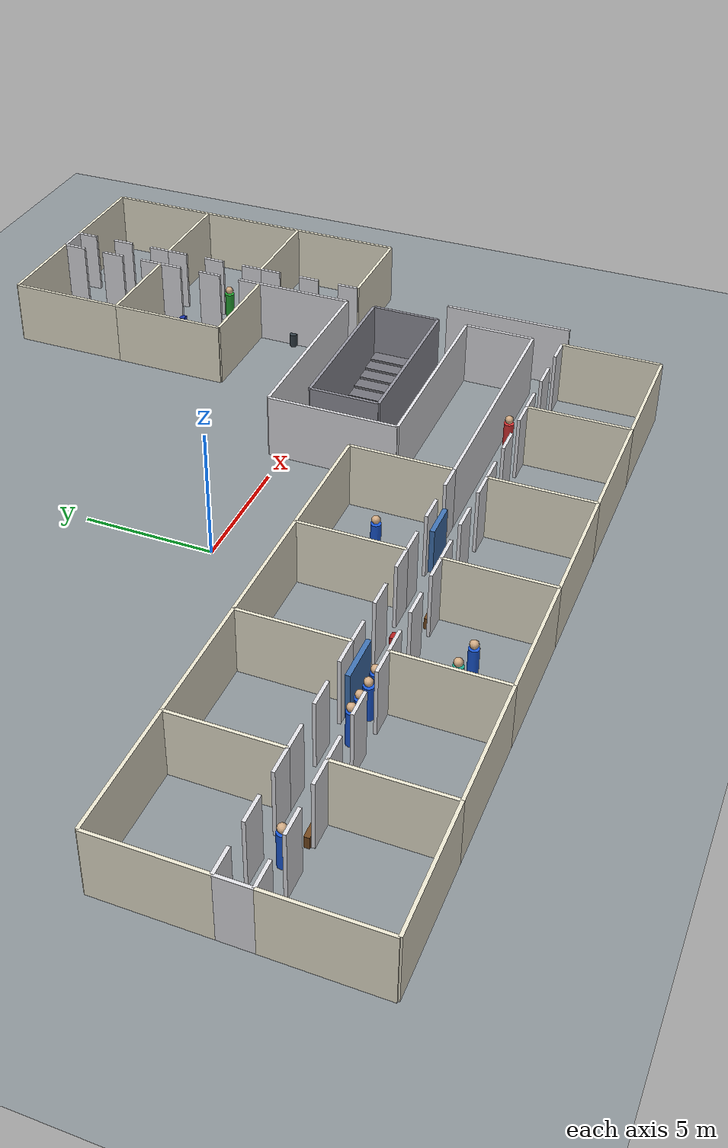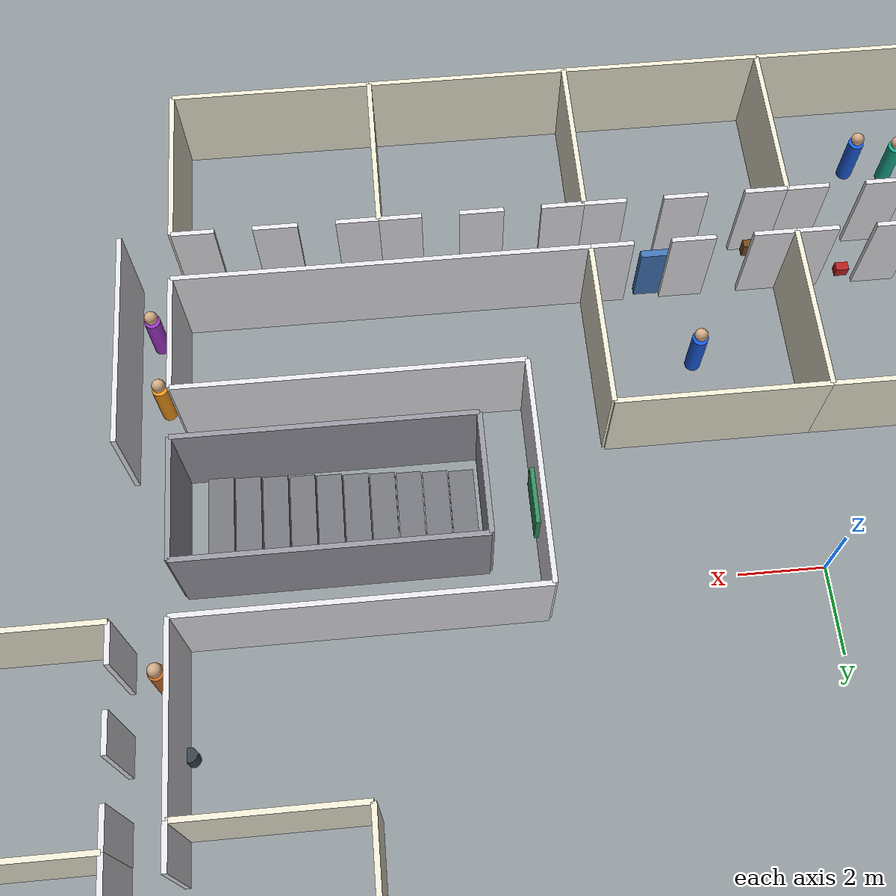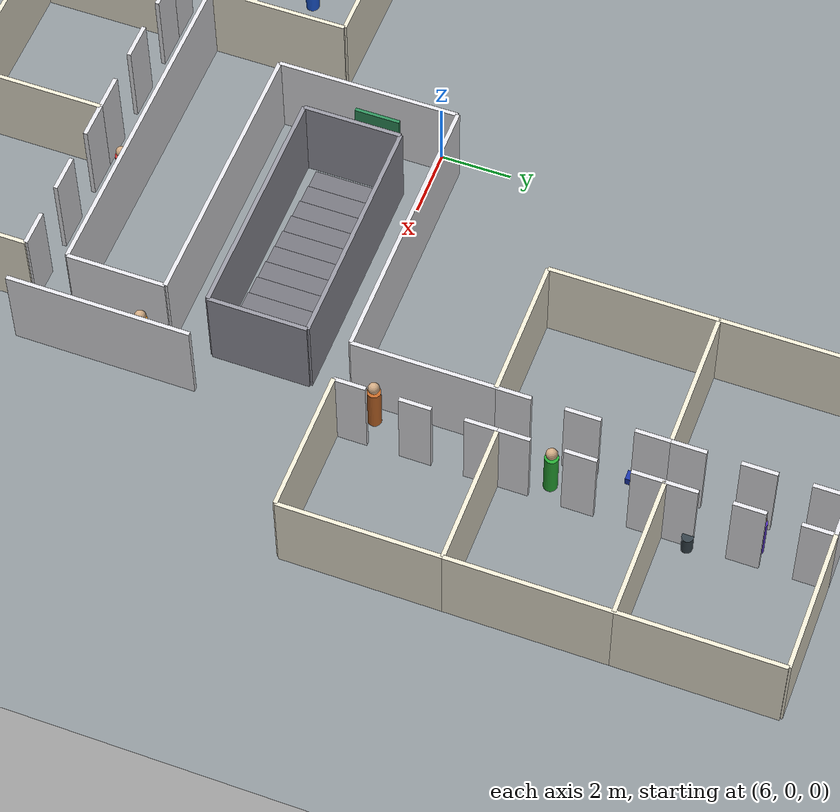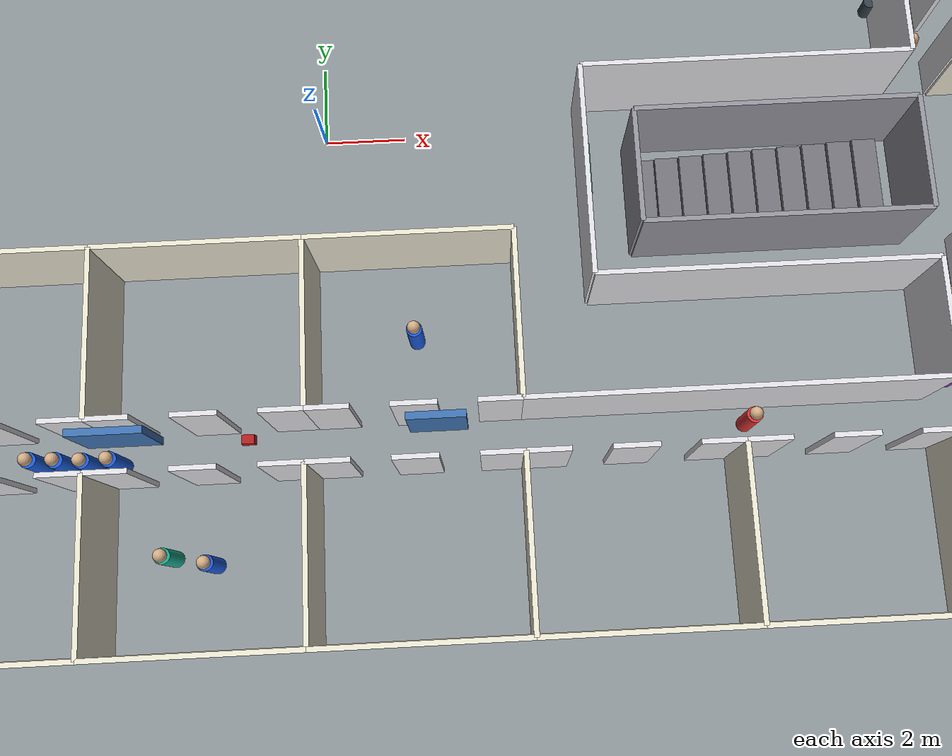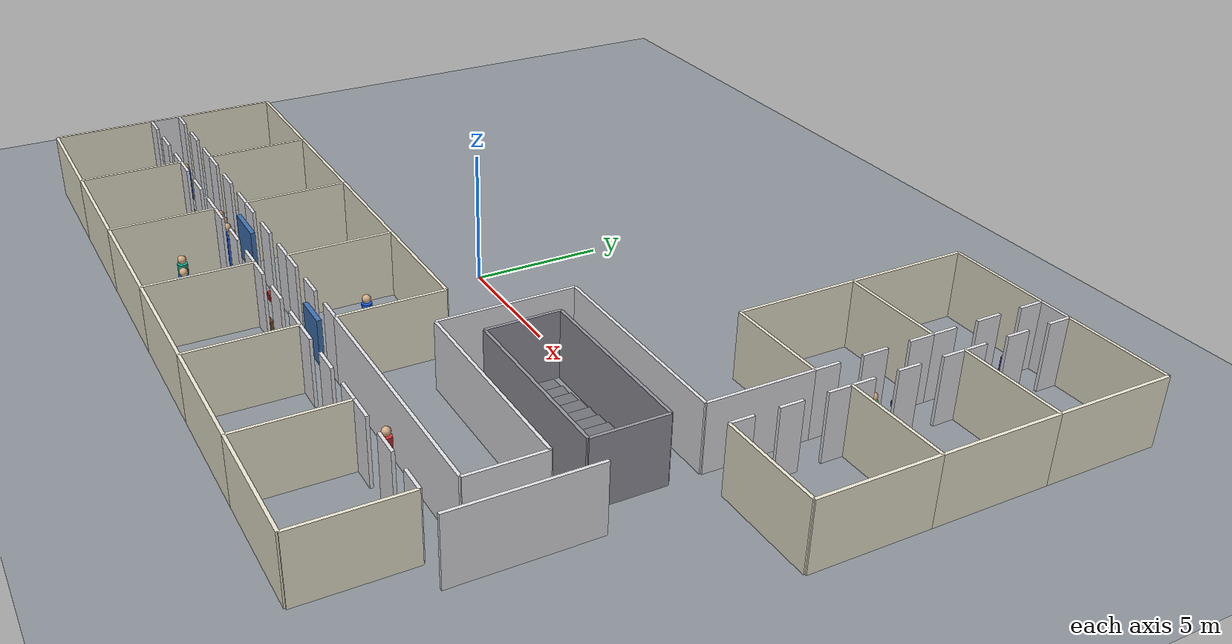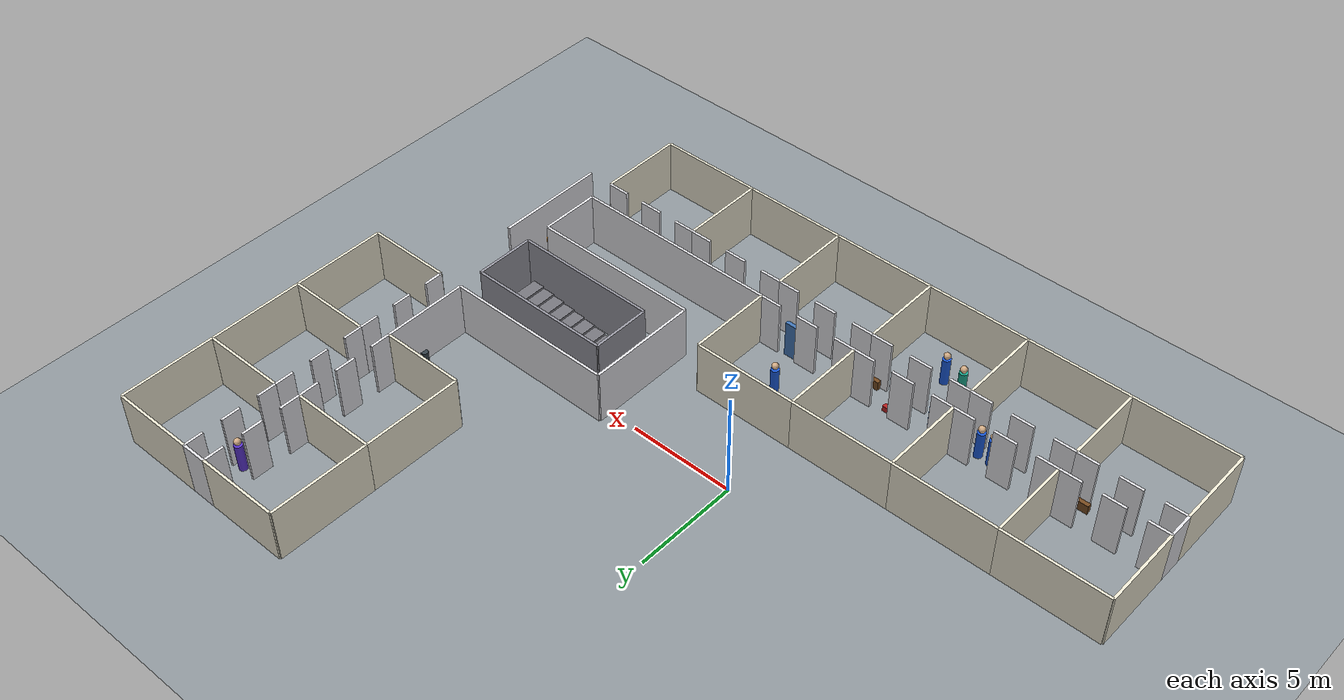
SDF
<?xml version='1.0' encoding='utf-8'?>
<sdf version="1.9">
  <world name="school_arena">
    <physics name="school_physics" type="ignored">
      <max_step_size>0.001</max_step_size>
      <real_time_factor>1.0</real_time_factor>
    </physics>
    <plugin filename="gz-sim-physics-system" name="gz::sim::systems::Physics" />
    <plugin filename="gz-sim-user-commands-system" name="gz::sim::systems::UserCommands" />
    <plugin filename="gz-sim-scene-broadcaster-system" name="gz::sim::systems::SceneBroadcaster" />
    <plugin filename="gz-sim-sensors-system" name="gz::sim::systems::Sensors">
      <render_engine>ogre2</render_engine>
    </plugin>
    <scene>
      <ambient>0.75 0.75 0.78 1</ambient>
      <background>0.92 0.95 1.0 1</background>
      <shadows>true</shadows>
    </scene>
    <light type="directional" name="sun">
      <pose>0 0 20 0 0 0</pose>
      <direction>-0.4 0.2 -1</direction>
      <diffuse>0.9 0.9 0.9 1</diffuse>
      <specular>0.2 0.2 0.2 1</specular>
    </light>
    <model name="ground">
      <static>true</static>
      <link name="link">
        <collision name="collision">
          <geometry>
            <plane>
              <normal>0 0 1</normal>
              <size>80 80</size>
            </plane>
          </geometry>
        </collision>
        <visual name="visual">
          <geometry>
            <plane>
              <normal>0 0 1</normal>
              <size>80 80</size>
            </plane>
          </geometry>
          <material>
            <ambient>0.55 0.58 0.60 1</ambient>
            <diffuse>0.55 0.58 0.60 1</diffuse>
          </material>
        </visual>
      </link>
    </model>
    <model name="classroom_01_south">
      <static>true</static>
      <pose>-12.5500 -12.6000 1.3000 0 0 0</pose>
      <link name="link">
        <collision name="collision">
          <geometry>
            <box>
              <size>4.9000 0.1200 2.6000</size>
            </box>
          </geometry>
        </collision>
        <visual name="visual">
          <geometry>
            <box>
              <size>4.9000 0.1200 2.6000</size>
            </box>
          </geometry>
          <material>
            <ambient>0.92 0.90 0.82 1</ambient>
            <diffuse>0.92 0.90 0.82 1</diffuse>
          </material>
        </visual>
      </link>
    </model>
    <model name="classroom_01_west">
      <static>true</static>
      <pose>-15.0000 -10.6000 1.3000 0 0 0</pose>
      <link name="link">
        <collision name="collision">
          <geometry>
            <box>
              <size>0.1200 4.0000 2.6000</size>
            </box>
          </geometry>
        </collision>
        <visual name="visual">
          <geometry>
            <box>
              <size>0.1200 4.0000 2.6000</size>
            </box>
          </geometry>
          <material>
            <ambient>0.92 0.90 0.82 1</ambient>
            <diffuse>0.92 0.90 0.82 1</diffuse>
          </material>
        </visual>
      </link>
    </model>
    <model name="classroom_01_east">
      <static>true</static>
      <pose>-10.1000 -10.6000 1.3000 0 0 0</pose>
      <link name="link">
        <collision name="collision">
          <geometry>
            <box>
              <size>0.1200 4.0000 2.6000</size>
            </box>
          </geometry>
        </collision>
        <visual name="visual">
          <geometry>
            <box>
              <size>0.1200 4.0000 2.6000</size>
            </box>
          </geometry>
          <material>
            <ambient>0.92 0.90 0.82 1</ambient>
            <diffuse>0.92 0.90 0.82 1</diffuse>
          </material>
        </visual>
      </link>
    </model>
    <model name="classroom_01_front_0">
      <static>true</static>
      <pose>-14.4900 -8.6000 1.3000 0 0 0</pose>
      <link name="link">
        <collision name="collision">
          <geometry>
            <box>
              <size>1.0200 0.1200 2.6000</size>
            </box>
          </geometry>
        </collision>
        <visual name="visual">
          <geometry>
            <box>
              <size>1.0200 0.1200 2.6000</size>
            </box>
          </geometry>
          <material>
            <ambient>0.88 0.88 0.90 1</ambient>
            <diffuse>0.88 0.88 0.90 1</diffuse>
          </material>
        </visual>
      </link>
    </model>
    <model name="classroom_01_front_1">
      <static>true</static>
      <pose>-12.5500 -8.6000 1.3000 0 0 0</pose>
      <link name="link">
        <collision name="collision">
          <geometry>
            <box>
              <size>1.0600 0.1200 2.6000</size>
            </box>
          </geometry>
        </collision>
        <visual name="visual">
          <geometry>
            <box>
              <size>1.0600 0.1200 2.6000</size>
            </box>
          </geometry>
          <material>
            <ambient>0.88 0.88 0.90 1</ambient>
            <diffuse>0.88 0.88 0.90 1</diffuse>
          </material>
        </visual>
      </link>
    </model>
    <model name="classroom_01_front_2">
      <static>true</static>
      <pose>-10.6100 -8.6000 1.3000 0 0 0</pose>
      <link name="link">
        <collision name="collision">
          <geometry>
            <box>
              <size>1.0200 0.1200 2.6000</size>
            </box>
          </geometry>
        </collision>
        <visual name="visual">
          <geometry>
            <box>
              <size>1.0200 0.1200 2.6000</size>
            </box>
          </geometry>
          <material>
            <ambient>0.88 0.88 0.90 1</ambient>
            <diffuse>0.88 0.88 0.90 1</diffuse>
          </material>
        </visual>
      </link>
    </model>
    <model name="classroom_02_south">
      <static>true</static>
      <pose>-7.6500 -12.6000 1.3000 0 0 0</pose>
      <link name="link">
        <collision name="collision">
          <geometry>
            <box>
              <size>4.9000 0.1200 2.6000</size>
            </box>
          </geometry>
        </collision>
        <visual name="visual">
          <geometry>
            <box>
              <size>4.9000 0.1200 2.6000</size>
            </box>
          </geometry>
          <material>
            <ambient>0.92 0.90 0.82 1</ambient>
            <diffuse>0.92 0.90 0.82 1</diffuse>
          </material>
        </visual>
      </link>
    </model>
    <model name="classroom_02_west">
      <static>true</static>
      <pose>-10.1000 -10.6000 1.3000 0 0 0</pose>
      <link name="link">
        <collision name="collision">
          <geometry>
            <box>
              <size>0.1200 4.0000 2.6000</size>
            </box>
          </geometry>
        </collision>
        <visual name="visual">
          <geometry>
            <box>
              <size>0.1200 4.0000 2.6000</size>
            </box>
          </geometry>
          <material>
            <ambient>0.92 0.90 0.82 1</ambient>
            <diffuse>0.92 0.90 0.82 1</diffuse>
          </material>
        </visual>
      </link>
    </model>
    <model name="classroom_02_east">
      <static>true</static>
      <pose>-5.2000 -10.6000 1.3000 0 0 0</pose>
      <link name="link">
        <collision name="collision">
          <geometry>
            <box>
              <size>0.1200 4.0000 2.6000</size>
            </box>
          </geometry>
        </collision>
        <visual name="visual">
          <geometry>
            <box>
              <size>0.1200 4.0000 2.6000</size>
            </box>
          </geometry>
          <material>
            <ambient>0.92 0.90 0.82 1</ambient>
            <diffuse>0.92 0.90 0.82 1</diffuse>
          </material>
        </visual>
      </link>
    </model>
    <model name="classroom_02_front_0">
      <static>true</static>
      <pose>-9.5900 -8.6000 1.3000 0 0 0</pose>
      <link name="link">
        <collision name="collision">
          <geometry>
            <box>
              <size>1.0200 0.1200 2.6000</size>
            </box>
          </geometry>
        </collision>
        <visual name="visual">
          <geometry>
            <box>
              <size>1.0200 0.1200 2.6000</size>
            </box>
          </geometry>
          <material>
            <ambient>0.88 0.88 0.90 1</ambient>
            <diffuse>0.88 0.88 0.90 1</diffuse>
          </material>
        </visual>
      </link>
    </model>
    <model name="classroom_02_front_1">
      <static>true</static>
      <pose>-7.6500 -8.6000 1.3000 0 0 0</pose>
      <link name="link">
        <collision name="collision">
          <geometry>
            <box>
              <size>1.0600 0.1200 2.6000</size>
            </box>
          </geometry>
        </collision>
        <visual name="visual">
          <geometry>
            <box>
              <size>1.0600 0.1200 2.6000</size>
            </box>
          </geometry>
          <material>
            <ambient>0.88 0.88 0.90 1</ambient>
            <diffuse>0.88 0.88 0.90 1</diffuse>
          </material>
        </visual>
      </link>
    </model>
    <model name="classroom_02_front_2">
      <static>true</static>
      <pose>-5.7100 -8.6000 1.3000 0 0 0</pose>
      <link name="link">
        <collision name="collision">
          <geometry>
            <box>
              <size>1.0200 0.1200 2.6000</size>
            </box>
          </geometry>
        </collision>
        <visual name="visual">
          <geometry>
            <box>
              <size>1.0200 0.1200 2.6000</size>
            </box>
          </geometry>
          <material>
            <ambient>0.88 0.88 0.90 1</ambient>
            <diffuse>0.88 0.88 0.90 1</diffuse>
          </material>
        </visual>
      </link>
    </model>
    <model name="classroom_03_south">
      <static>true</static>
      <pose>-2.7500 -12.6000 1.3000 0 0 0</pose>
      <link name="link">
        <collision name="collision">
          <geometry>
            <box>
              <size>4.9000 0.1200 2.6000</size>
            </box>
          </geometry>
        </collision>
        <visual name="visual">
          <geometry>
            <box>
              <size>4.9000 0.1200 2.6000</size>
            </box>
          </geometry>
          <material>
            <ambient>0.92 0.90 0.82 1</ambient>
            <diffuse>0.92 0.90 0.82 1</diffuse>
          </material>
        </visual>
      </link>
    </model>
    <model name="classroom_03_west">
      <static>true</static>
      <pose>-5.2000 -10.6000 1.3000 0 0 0</pose>
      <link name="link">
        <collision name="collision">
          <geometry>
            <box>
              <size>0.1200 4.0000 2.6000</size>
            </box>
          </geometry>
        </collision>
        <visual name="visual">
          <geometry>
            <box>
              <size>0.1200 4.0000 2.6000</size>
            </box>
          </geometry>
          <material>
            <ambient>0.92 0.90 0.82 1</ambient>
            <diffuse>0.92 0.90 0.82 1</diffuse>
          </material>
        </visual>
      </link>
    </model>
    <model name="classroom_03_east">
      <static>true</static>
      <pose>-0.3000 -10.6000 1.3000 0 0 0</pose>
      <link name="link">
        <collision name="collision">
          <geometry>
            <box>
              <size>0.1200 4.0000 2.6000</size>
            </box>
          </geometry>
        </collision>
        <visual name="visual">
          <geometry>
            <box>
              <size>0.1200 4.0000 2.6000</size>
            </box>
          </geometry>
          <material>
            <ambient>0.92 0.90 0.82 1</ambient>
            <diffuse>0.92 0.90 0.82 1</diffuse>
          </material>
        </visual>
      </link>
    </model>
    <model name="classroom_03_front_0">
      <static>true</static>
      <pose>-4.6900 -8.6000 1.3000 0 0 0</pose>
      <link name="link">
        <collision name="collision">
          <geometry>
            <box>
              <size>1.0200 0.1200 2.6000</size>
            </box>
          </geometry>
        </collision>
        <visual name="visual">
          <geometry>
            <box>
              <size>1.0200 0.1200 2.6000</size>
            </box>
          </geometry>
          <material>
            <ambient>0.88 0.88 0.90 1</ambient>
            <diffuse>0.88 0.88 0.90 1</diffuse>
          </material>
        </visual>
      </link>
    </model>
    <model name="classroom_03_front_1">
      <static>true</static>
      <pose>-2.7500 -8.6000 1.3000 0 0 0</pose>
      <link name="link">
        <collision name="collision">
          <geometry>
            <box>
              <size>1.0600 0.1200 2.6000</size>
            </box>
          </geometry>
        </collision>
        <visual name="visual">
          <geometry>
            <box>
              <size>1.0600 0.1200 2.6000</size>
            </box>
          </geometry>
          <material>
            <ambient>0.88 0.88 0.90 1</ambient>
            <diffuse>0.88 0.88 0.90 1</diffuse>
          </material>
        </visual>
      </link>
    </model>
    <model name="classroom_03_front_2">
      <static>true</static>
      <pose>-0.8100 -8.6000 1.3000 0 0 0</pose>
      <link name="link">
        <collision name="collision">
          <geometry>
            <box>
              <size>1.0200 0.1200 2.6000</size>
            </box>
          </geometry>
        </collision>
        <visual name="visual">
          <geometry>
            <box>
              <size>1.0200 0.1200 2.6000</size>
            </box>
          </geometry>
          <material>
            <ambient>0.88 0.88 0.90 1</ambient>
            <diffuse>0.88 0.88 0.90 1</diffuse>
          </material>
        </visual>
      </link>
    </model>
    <model name="classroom_04_south">
      <static>true</static>
      <pose>2.1500 -12.6000 1.3000 0 0 0</pose>
      <link name="link">
        <collision name="collision">
          <geometry>
            <box>
              <size>4.9000 0.1200 2.6000</size>
            </box>
          </geometry>
        </collision>
        <visual name="visual">
          <geometry>
            <box>
              <size>4.9000 0.1200 2.6000</size>
            </box>
          </geometry>
          <material>
            <ambient>0.92 0.90 0.82 1</ambient>
            <diffuse>0.92 0.90 0.82 1</diffuse>
          </material>
        </visual>
      </link>
    </model>
    <model name="classroom_04_west">
      <static>true</static>
      <pose>-0.3000 -10.6000 1.3000 0 0 0</pose>
      <link name="link">
        <collision name="collision">
          <geometry>
            <box>
              <size>0.1200 4.0000 2.6000</size>
            </box>
          </geometry>
        </collision>
        <visual name="visual">
          <geometry>
            <box>
              <size>0.1200 4.0000 2.6000</size>
            </box>
          </geometry>
          <material>
            <ambient>0.92 0.90 0.82 1</ambient>
            <diffuse>0.92 0.90 0.82 1</diffuse>
          </material>
        </visual>
      </link>
    </model>
    <model name="classroom_04_east">
      <static>true</static>
      <pose>4.6000 -10.6000 1.3000 0 0 0</pose>
      <link name="link">
        <collision name="collision">
          <geometry>
            <box>
              <size>0.1200 4.0000 2.6000</size>
            </box>
          </geometry>
        </collision>
        <visual name="visual">
          <geometry>
            <box>
              <size>0.1200 4.0000 2.6000</size>
            </box>
          </geometry>
          <material>
            <ambient>0.92 0.90 0.82 1</ambient>
            <diffuse>0.92 0.90 0.82 1</diffuse>
          </material>
        </visual>
      </link>
    </model>
    <model name="classroom_04_front_0">
      <static>true</static>
      <pose>0.2100 -8.6000 1.3000 0 0 0</pose>
      <link name="link">
        <collision name="collision">
          <geometry>
            <box>
              <size>1.0200 0.1200 2.6000</size>
            </box>
          </geometry>
        </collision>
        <visual name="visual">
          <geometry>
            <box>
              <size>1.0200 0.1200 2.6000</size>
            </box>
          </geometry>
          <material>
            <ambient>0.88 0.88 0.90 1</ambient>
            <diffuse>0.88 0.88 0.90 1</diffuse>
          </material>
        </visual>
      </link>
    </model>
    <model name="classroom_04_front_1">
      <static>true</static>
      <pose>2.1500 -8.6000 1.3000 0 0 0</pose>
      <link name="link">
        <collision name="collision">
          <geometry>
            <box>
              <size>1.0600 0.1200 2.6000</size>
            </box>
          </geometry>
        </collision>
        <visual name="visual">
          <geometry>
            <box>
              <size>1.0600 0.1200 2.6000</size>
            </box>
          </geometry>
          <material>
            <ambient>0.88 0.88 0.90 1</ambient>
            <diffuse>0.88 0.88 0.90 1</diffuse>
          </material>
        </visual>
      </link>
    </model>
    <model name="classroom_04_front_2">
      <static>true</static>
      <pose>4.0900 -8.6000 1.3000 0 0 0</pose>
      <link name="link">
        <collision name="collision">
          <geometry>
            <box>
              <size>1.0200 0.1200 2.6000</size>
            </box>
          </geometry>
        </collision>
        <visual name="visual">
          <geometry>
            <box>
              <size>1.0200 0.1200 2.6000</size>
            </box>
          </geometry>
          <material>
            <ambient>0.88 0.88 0.90 1</ambient>
            <diffuse>0.88 0.88 0.90 1</diffuse>
          </material>
        </visual>
      </link>
    </model>
    <model name="classroom_05_south">
      <static>true</static>
      <pose>7.0500 -12.6000 1.3000 0 0 0</pose>
      <link name="link">
        <collision name="collision">
          <geometry>
            <box>
              <size>4.9000 0.1200 2.6000</size>
            </box>
          </geometry>
        </collision>
        <visual name="visual">
          <geometry>
            <box>
              <size>4.9000 0.1200 2.6000</size>
            </box>
          </geometry>
          <material>
            <ambient>0.92 0.90 0.82 1</ambient>
            <diffuse>0.92 0.90 0.82 1</diffuse>
          </material>
        </visual>
      </link>
    </model>
    <model name="classroom_05_west">
      <static>true</static>
      <pose>4.6000 -10.6000 1.3000 0 0 0</pose>
      <link name="link">
        <collision name="collision">
          <geometry>
            <box>
              <size>0.1200 4.0000 2.6000</size>
            </box>
          </geometry>
        </collision>
        <visual name="visual">
          <geometry>
            <box>
              <size>0.1200 4.0000 2.6000</size>
            </box>
          </geometry>
          <material>
            <ambient>0.92 0.90 0.82 1</ambient>
            <diffuse>0.92 0.90 0.82 1</diffuse>
          </material>
        </visual>
      </link>
    </model>
    <model name="classroom_05_east">
      <static>true</static>
      <pose>9.5000 -10.6000 1.3000 0 0 0</pose>
      <link name="link">
        <collision name="collision">
          <geometry>
            <box>
              <size>0.1200 4.0000 2.6000</size>
            </box>
          </geometry>
        </collision>
        <visual name="visual">
          <geometry>
            <box>
              <size>0.1200 4.0000 2.6000</size>
            </box>
          </geometry>
          <material>
            <ambient>0.92 0.90 0.82 1</ambient>
            <diffuse>0.92 0.90 0.82 1</diffuse>
          </material>
        </visual>
      </link>
    </model>
    <model name="classroom_05_front_0">
      <static>true</static>
      <pose>5.1100 -8.6000 1.3000 0 0 0</pose>
      <link name="link">
        <collision name="collision">
          <geometry>
            <box>
              <size>1.0200 0.1200 2.6000</size>
            </box>
          </geometry>
        </collision>
        <visual name="visual">
          <geometry>
            <box>
              <size>1.0200 0.1200 2.6000</size>
            </box>
          </geometry>
          <material>
            <ambient>0.88 0.88 0.90 1</ambient>
            <diffuse>0.88 0.88 0.90 1</diffuse>
          </material>
        </visual>
      </link>
    </model>
    <model name="classroom_05_front_1">
      <static>true</static>
      <pose>7.0500 -8.6000 1.3000 0 0 0</pose>
      <link name="link">
        <collision name="collision">
          <geometry>
            <box>
              <size>1.0600 0.1200 2.6000</size>
            </box>
          </geometry>
        </collision>
        <visual name="visual">
          <geometry>
            <box>
              <size>1.0600 0.1200 2.6000</size>
            </box>
          </geometry>
          <material>
            <ambient>0.88 0.88 0.90 1</ambient>
            <diffuse>0.88 0.88 0.90 1</diffuse>
          </material>
        </visual>
      </link>
    </model>
    <model name="classroom_05_front_2">
      <static>true</static>
      <pose>8.9900 -8.6000 1.3000 0 0 0</pose>
      <link name="link">
        <collision name="collision">
          <geometry>
            <box>
              <size>1.0200 0.1200 2.6000</size>
            </box>
          </geometry>
        </collision>
        <visual name="visual">
          <geometry>
            <box>
              <size>1.0200 0.1200 2.6000</size>
            </box>
          </geometry>
          <material>
            <ambient>0.88 0.88 0.90 1</ambient>
            <diffuse>0.88 0.88 0.90 1</diffuse>
          </material>
        </visual>
      </link>
    </model>
    <model name="classroom_06_south">
      <static>true</static>
      <pose>11.9500 -12.6000 1.3000 0 0 0</pose>
      <link name="link">
        <collision name="collision">
          <geometry>
            <box>
              <size>4.9000 0.1200 2.6000</size>
            </box>
          </geometry>
        </collision>
        <visual name="visual">
          <geometry>
            <box>
              <size>4.9000 0.1200 2.6000</size>
            </box>
          </geometry>
          <material>
            <ambient>0.92 0.90 0.82 1</ambient>
            <diffuse>0.92 0.90 0.82 1</diffuse>
          </material>
        </visual>
      </link>
    </model>
    <model name="classroom_06_west">
      <static>true</static>
      <pose>9.5000 -10.6000 1.3000 0 0 0</pose>
      <link name="link">
        <collision name="collision">
          <geometry>
            <box>
              <size>0.1200 4.0000 2.6000</size>
            </box>
          </geometry>
        </collision>
        <visual name="visual">
          <geometry>
            <box>
              <size>0.1200 4.0000 2.6000</size>
            </box>
          </geometry>
          <material>
            <ambient>0.92 0.90 0.82 1</ambient>
            <diffuse>0.92 0.90 0.82 1</diffuse>
          </material>
        </visual>
      </link>
    </model>
    <model name="classroom_06_east">
      <static>true</static>
      <pose>14.4000 -10.6000 1.3000 0 0 0</pose>
      <link name="link">
        <collision name="collision">
          <geometry>
            <box>
              <size>0.1200 4.0000 2.6000</size>
            </box>
          </geometry>
        </collision>
        <visual name="visual">
          <geometry>
            <box>
              <size>0.1200 4.0000 2.6000</size>
            </box>
          </geometry>
          <material>
            <ambient>0.92 0.90 0.82 1</ambient>
            <diffuse>0.92 0.90 0.82 1</diffuse>
          </material>
        </visual>
      </link>
    </model>
    <model name="classroom_06_front_0">
      <static>true</static>
      <pose>10.0100 -8.6000 1.3000 0 0 0</pose>
      <link name="link">
        <collision name="collision">
          <geometry>
            <box>
              <size>1.0200 0.1200 2.6000</size>
            </box>
          </geometry>
        </collision>
        <visual name="visual">
          <geometry>
            <box>
              <size>1.0200 0.1200 2.6000</size>
            </box>
          </geometry>
          <material>
            <ambient>0.88 0.88 0.90 1</ambient>
            <diffuse>0.88 0.88 0.90 1</diffuse>
          </material>
        </visual>
      </link>
    </model>
    <model name="classroom_06_front_1">
      <static>true</static>
      <pose>11.9500 -8.6000 1.3000 0 0 0</pose>
      <link name="link">
        <collision name="collision">
          <geometry>
            <box>
              <size>1.0600 0.1200 2.6000</size>
            </box>
          </geometry>
        </collision>
        <visual name="visual">
          <geometry>
            <box>
              <size>1.0600 0.1200 2.6000</size>
            </box>
          </geometry>
          <material>
            <ambient>0.88 0.88 0.90 1</ambient>
            <diffuse>0.88 0.88 0.90 1</diffuse>
          </material>
        </visual>
      </link>
    </model>
    <model name="classroom_06_front_2">
      <static>true</static>
      <pose>13.8900 -8.6000 1.3000 0 0 0</pose>
      <link name="link">
        <collision name="collision">
          <geometry>
            <box>
              <size>1.0200 0.1200 2.6000</size>
            </box>
          </geometry>
        </collision>
        <visual name="visual">
          <geometry>
            <box>
              <size>1.0200 0.1200 2.6000</size>
            </box>
          </geometry>
          <material>
            <ambient>0.88 0.88 0.90 1</ambient>
            <diffuse>0.88 0.88 0.90 1</diffuse>
          </material>
        </visual>
      </link>
    </model>
    <model name="classroom_07_north">
      <static>true</static>
      <pose>-12.5500 -3.4000 1.3000 0 0 0</pose>
      <link name="link">
        <collision name="collision">
          <geometry>
            <box>
              <size>4.9000 0.1200 2.6000</size>
            </box>
          </geometry>
        </collision>
        <visual name="visual">
          <geometry>
            <box>
              <size>4.9000 0.1200 2.6000</size>
            </box>
          </geometry>
          <material>
            <ambient>0.92 0.90 0.82 1</ambient>
            <diffuse>0.92 0.90 0.82 1</diffuse>
          </material>
        </visual>
      </link>
    </model>
    <model name="classroom_07_west">
      <static>true</static>
      <pose>-15.0000 -5.4000 1.3000 0 0 0</pose>
      <link name="link">
        <collision name="collision">
          <geometry>
            <box>
              <size>0.1200 4.0000 2.6000</size>
            </box>
          </geometry>
        </collision>
        <visual name="visual">
          <geometry>
            <box>
              <size>0.1200 4.0000 2.6000</size>
            </box>
          </geometry>
          <material>
            <ambient>0.92 0.90 0.82 1</ambient>
            <diffuse>0.92 0.90 0.82 1</diffuse>
          </material>
        </visual>
      </link>
    </model>
    <model name="classroom_07_east">
      <static>true</static>
      <pose>-10.1000 -5.4000 1.3000 0 0 0</pose>
      <link name="link">
        <collision name="collision">
          <geometry>
            <box>
              <size>0.1200 4.0000 2.6000</size>
            </box>
          </geometry>
        </collision>
        <visual name="visual">
          <geometry>
            <box>
              <size>0.1200 4.0000 2.6000</size>
            </box>
          </geometry>
          <material>
            <ambient>0.92 0.90 0.82 1</ambient>
            <diffuse>0.92 0.90 0.82 1</diffuse>
          </material>
        </visual>
      </link>
    </model>
    <model name="classroom_07_front_0">
      <static>true</static>
      <pose>-14.4900 -7.4000 1.3000 0 0 0</pose>
      <link name="link">
        <collision name="collision">
          <geometry>
            <box>
              <size>1.0200 0.1200 2.6000</size>
            </box>
          </geometry>
        </collision>
        <visual name="visual">
          <geometry>
            <box>
              <size>1.0200 0.1200 2.6000</size>
            </box>
          </geometry>
          <material>
            <ambient>0.88 0.88 0.90 1</ambient>
            <diffuse>0.88 0.88 0.90 1</diffuse>
          </material>
        </visual>
      </link>
    </model>
    <model name="classroom_07_front_1">
      <static>true</static>
      <pose>-12.5500 -7.4000 1.3000 0 0 0</pose>
      <link name="link">
        <collision name="collision">
          <geometry>
            <box>
              <size>1.0600 0.1200 2.6000</size>
            </box>
          </geometry>
        </collision>
        <visual name="visual">
          <geometry>
            <box>
              <size>1.0600 0.1200 2.6000</size>
            </box>
          </geometry>
          <material>
            <ambient>0.88 0.88 0.90 1</ambient>
            <diffuse>0.88 0.88 0.90 1</diffuse>
          </material>
        </visual>
      </link>
    </model>
    <model name="classroom_07_front_2">
      <static>true</static>
      <pose>-10.6100 -7.4000 1.3000 0 0 0</pose>
      <link name="link">
        <collision name="collision">
          <geometry>
            <box>
              <size>1.0200 0.1200 2.6000</size>
            </box>
          </geometry>
        </collision>
        <visual name="visual">
          <geometry>
            <box>
              <size>1.0200 0.1200 2.6000</size>
            </box>
          </geometry>
          <material>
            <ambient>0.88 0.88 0.90 1</ambient>
            <diffuse>0.88 0.88 0.90 1</diffuse>
          </material>
        </visual>
      </link>
    </model>
    <model name="classroom_08_north">
      <static>true</static>
      <pose>-7.6500 -3.4000 1.3000 0 0 0</pose>
      <link name="link">
        <collision name="collision">
          <geometry>
            <box>
              <size>4.9000 0.1200 2.6000</size>
            </box>
          </geometry>
        </collision>
        <visual name="visual">
          <geometry>
            <box>
              <size>4.9000 0.1200 2.6000</size>
            </box>
          </geometry>
          <material>
            <ambient>0.92 0.90 0.82 1</ambient>
            <diffuse>0.92 0.90 0.82 1</diffuse>
          </material>
        </visual>
      </link>
    </model>
    <model name="classroom_08_west">
      <static>true</static>
      <pose>-10.1000 -5.4000 1.3000 0 0 0</pose>
      <link name="link">
        <collision name="collision">
          <geometry>
            <box>
              <size>0.1200 4.0000 2.6000</size>
            </box>
          </geometry>
        </collision>
        <visual name="visual">
          <geometry>
            <box>
              <size>0.1200 4.0000 2.6000</size>
            </box>
          </geometry>
          <material>
            <ambient>0.92 0.90 0.82 1</ambient>
            <diffuse>0.92 0.90 0.82 1</diffuse>
          </material>
        </visual>
      </link>
    </model>
    <model name="classroom_08_east">
      <static>true</static>
      <pose>-5.2000 -5.4000 1.3000 0 0 0</pose>
      <link name="link">
        <collision name="collision">
          <geometry>
            <box>
              <size>0.1200 4.0000 2.6000</size>
            </box>
          </geometry>
        </collision>
        <visual name="visual">
          <geometry>
            <box>
              <size>0.1200 4.0000 2.6000</size>
            </box>
          </geometry>
          <material>
            <ambient>0.92 0.90 0.82 1</ambient>
            <diffuse>0.92 0.90 0.82 1</diffuse>
          </material>
        </visual>
      </link>
    </model>
    <model name="classroom_08_front_0">
      <static>true</static>
      <pose>-9.5900 -7.4000 1.3000 0 0 0</pose>
      <link name="link">
        <collision name="collision">
          <geometry>
            <box>
              <size>1.0200 0.1200 2.6000</size>
            </box>
          </geometry>
        </collision>
        <visual name="visual">
          <geometry>
            <box>
              <size>1.0200 0.1200 2.6000</size>
            </box>
          </geometry>
          <material>
            <ambient>0.88 0.88 0.90 1</ambient>
            <diffuse>0.88 0.88 0.90 1</diffuse>
          </material>
        </visual>
      </link>
    </model>
    <model name="classroom_08_front_1">
      <static>true</static>
      <pose>-7.6500 -7.4000 1.3000 0 0 0</pose>
      <link name="link">
        <collision name="collision">
          <geometry>
            <box>
              <size>1.0600 0.1200 2.6000</size>
            </box>
          </geometry>
        </collision>
        <visual name="visual">
          <geometry>
            <box>
              <size>1.0600 0.1200 2.6000</size>
            </box>
          </geometry>
          <material>
            <ambient>0.88 0.88 0.90 1</ambient>
            <diffuse>0.88 0.88 0.90 1</diffuse>
          </material>
        </visual>
      </link>
    </model>
    <model name="classroom_08_front_2">
      <static>true</static>
      <pose>-5.7100 -7.4000 1.3000 0 0 0</pose>
      <link name="link">
        <collision name="collision">
          <geometry>
            <box>
              <size>1.0200 0.1200 2.6000</size>
            </box>
          </geometry>
        </collision>
        <visual name="visual">
          <geometry>
            <box>
              <size>1.0200 0.1200 2.6000</size>
            </box>
          </geometry>
          <material>
            <ambient>0.88 0.88 0.90 1</ambient>
            <diffuse>0.88 0.88 0.90 1</diffuse>
          </material>
        </visual>
      </link>
    </model>
    <model name="classroom_09_north">
      <static>true</static>
      <pose>-2.7500 -3.4000 1.3000 0 0 0</pose>
      <link name="link">
        <collision name="collision">
          <geometry>
            <box>
              <size>4.9000 0.1200 2.6000</size>
            </box>
          </geometry>
        </collision>
        <visual name="visual">
          <geometry>
            <box>
              <size>4.9000 0.1200 2.6000</size>
            </box>
          </geometry>
          <material>
            <ambient>0.92 0.90 0.82 1</ambient>
            <diffuse>0.92 0.90 0.82 1</diffuse>
          </material>
        </visual>
      </link>
    </model>
    <model name="classroom_09_west">
      <static>true</static>
      <pose>-5.2000 -5.4000 1.3000 0 0 0</pose>
      <link name="link">
        <collision name="collision">
          <geometry>
            <box>
              <size>0.1200 4.0000 2.6000</size>
            </box>
          </geometry>
        </collision>
        <visual name="visual">
          <geometry>
            <box>
              <size>0.1200 4.0000 2.6000</size>
            </box>
          </geometry>
          <material>
            <ambient>0.92 0.90 0.82 1</ambient>
            <diffuse>0.92 0.90 0.82 1</diffuse>
          </material>
        </visual>
      </link>
    </model>
    <model name="classroom_09_east">
      <static>true</static>
      <pose>-0.3000 -5.4000 1.3000 0 0 0</pose>
      <link name="link">
        <collision name="collision">
          <geometry>
            <box>
              <size>0.1200 4.0000 2.6000</size>
            </box>
          </geometry>
        </collision>
        <visual name="visual">
          <geometry>
            <box>
              <size>0.1200 4.0000 2.6000</size>
            </box>
          </geometry>
          <material>
            <ambient>0.92 0.90 0.82 1</ambient>
            <diffuse>0.92 0.90 0.82 1</diffuse>
          </material>
        </visual>
      </link>
    </model>
    <model name="classroom_09_front_0">
      <static>true</static>
      <pose>-4.6900 -7.4000 1.3000 0 0 0</pose>
      <link name="link">
        <collision name="collision">
          <geometry>
            <box>
              <size>1.0200 0.1200 2.6000</size>
            </box>
          </geometry>
        </collision>
        <visual name="visual">
          <geometry>
            <box>
              <size>1.0200 0.1200 2.6000</size>
            </box>
          </geometry>
          <material>
            <ambient>0.88 0.88 0.90 1</ambient>
            <diffuse>0.88 0.88 0.90 1</diffuse>
          </material>
        </visual>
      </link>
    </model>
    <model name="classroom_09_front_1">
      <static>true</static>
      <pose>-2.7500 -7.4000 1.3000 0 0 0</pose>
      <link name="link">
        <collision name="collision">
          <geometry>
            <box>
              <size>1.0600 0.1200 2.6000</size>
            </box>
          </geometry>
        </collision>
        <visual name="visual">
          <geometry>
            <box>
              <size>1.0600 0.1200 2.6000</size>
            </box>
          </geometry>
          <material>
            <ambient>0.88 0.88 0.90 1</ambient>
            <diffuse>0.88 0.88 0.90 1</diffuse>
          </material>
        </visual>
      </link>
    </model>
    <model name="classroom_09_front_2">
      <static>true</static>
      <pose>-0.8100 -7.4000 1.3000 0 0 0</pose>
      <link name="link">
        <collision name="collision">
          <geometry>
            <box>
              <size>1.0200 0.1200 2.6000</size>
            </box>
          </geometry>
        </collision>
        <visual name="visual">
          <geometry>
            <box>
              <size>1.0200 0.1200 2.6000</size>
            </box>
          </geometry>
          <material>
            <ambient>0.88 0.88 0.90 1</ambient>
            <diffuse>0.88 0.88 0.90 1</diffuse>
          </material>
        </visual>
      </link>
    </model>
    <model name="classroom_10_north">
      <static>true</static>
      <pose>2.1500 -3.4000 1.3000 0 0 0</pose>
      <link name="link">
        <collision name="collision">
          <geometry>
            <box>
              <size>4.9000 0.1200 2.6000</size>
            </box>
          </geometry>
        </collision>
        <visual name="visual">
          <geometry>
            <box>
              <size>4.9000 0.1200 2.6000</size>
            </box>
          </geometry>
          <material>
            <ambient>0.92 0.90 0.82 1</ambient>
            <diffuse>0.92 0.90 0.82 1</diffuse>
          </material>
        </visual>
      </link>
    </model>
    <model name="classroom_10_west">
      <static>true</static>
      <pose>-0.3000 -5.4000 1.3000 0 0 0</pose>
      <link name="link">
        <collision name="collision">
          <geometry>
            <box>
              <size>0.1200 4.0000 2.6000</size>
            </box>
          </geometry>
        </collision>
        <visual name="visual">
          <geometry>
            <box>
              <size>0.1200 4.0000 2.6000</size>
            </box>
          </geometry>
          <material>
            <ambient>0.92 0.90 0.82 1</ambient>
            <diffuse>0.92 0.90 0.82 1</diffuse>
          </material>
        </visual>
      </link>
    </model>
    <model name="classroom_10_east">
      <static>true</static>
      <pose>4.6000 -5.4000 1.3000 0 0 0</pose>
      <link name="link">
        <collision name="collision">
          <geometry>
            <box>
              <size>0.1200 4.0000 2.6000</size>
            </box>
          </geometry>
        </collision>
        <visual name="visual">
          <geometry>
            <box>
              <size>0.1200 4.0000 2.6000</size>
            </box>
          </geometry>
          <material>
            <ambient>0.92 0.90 0.82 1</ambient>
            <diffuse>0.92 0.90 0.82 1</diffuse>
          </material>
        </visual>
      </link>
    </model>
    <model name="classroom_10_front_0">
      <static>true</static>
      <pose>0.2100 -7.4000 1.3000 0 0 0</pose>
      <link name="link">
        <collision name="collision">
          <geometry>
            <box>
              <size>1.0200 0.1200 2.6000</size>
            </box>
          </geometry>
        </collision>
        <visual name="visual">
          <geometry>
            <box>
              <size>1.0200 0.1200 2.6000</size>
            </box>
          </geometry>
          <material>
            <ambient>0.88 0.88 0.90 1</ambient>
            <diffuse>0.88 0.88 0.90 1</diffuse>
          </material>
        </visual>
      </link>
    </model>
    <model name="classroom_10_front_1">
      <static>true</static>
      <pose>2.1500 -7.4000 1.3000 0 0 0</pose>
      <link name="link">
        <collision name="collision">
          <geometry>
            <box>
              <size>1.0600 0.1200 2.6000</size>
            </box>
          </geometry>
        </collision>
        <visual name="visual">
          <geometry>
            <box>
              <size>1.0600 0.1200 2.6000</size>
            </box>
          </geometry>
          <material>
            <ambient>0.88 0.88 0.90 1</ambient>
            <diffuse>0.88 0.88 0.90 1</diffuse>
          </material>
        </visual>
      </link>
    </model>
    <model name="classroom_10_front_2">
      <static>true</static>
      <pose>4.0900 -7.4000 1.3000 0 0 0</pose>
      <link name="link">
        <collision name="collision">
          <geometry>
            <box>
              <size>1.0200 0.1200 2.6000</size>
            </box>
          </geometry>
        </collision>
        <visual name="visual">
          <geometry>
            <box>
              <size>1.0200 0.1200 2.6000</size>
            </box>
          </geometry>
          <material>
            <ambient>0.88 0.88 0.90 1</ambient>
            <diffuse>0.88 0.88 0.90 1</diffuse>
          </material>
        </visual>
      </link>
    </model>
    <model name="classroom_11_south">
      <static>true</static>
      <pose>17.6000 0.6000 1.3000 0 0 0</pose>
      <link name="link">
        <collision name="collision">
          <geometry>
            <box>
              <size>4.0000 0.1200 2.6000</size>
            </box>
          </geometry>
        </collision>
        <visual name="visual">
          <geometry>
            <box>
              <size>4.0000 0.1200 2.6000</size>
            </box>
          </geometry>
          <material>
            <ambient>0.92 0.90 0.82 1</ambient>
            <diffuse>0.92 0.90 0.82 1</diffuse>
          </material>
        </visual>
      </link>
    </model>
    <model name="classroom_11_north">
      <static>true</static>
      <pose>17.6000 5.0667 1.3000 0 0 0</pose>
      <link name="link">
        <collision name="collision">
          <geometry>
            <box>
              <size>4.0000 0.1200 2.6000</size>
            </box>
          </geometry>
        </collision>
        <visual name="visual">
          <geometry>
            <box>
              <size>4.0000 0.1200 2.6000</size>
            </box>
          </geometry>
          <material>
            <ambient>0.92 0.90 0.82 1</ambient>
            <diffuse>0.92 0.90 0.82 1</diffuse>
          </material>
        </visual>
      </link>
    </model>
    <model name="classroom_11_east">
      <static>true</static>
      <pose>19.6000 2.8333 1.3000 0 0 0</pose>
      <link name="link">
        <collision name="collision">
          <geometry>
            <box>
              <size>0.1200 4.4667 2.6000</size>
            </box>
          </geometry>
        </collision>
        <visual name="visual">
          <geometry>
            <box>
              <size>0.1200 4.4667 2.6000</size>
            </box>
          </geometry>
          <material>
            <ambient>0.92 0.90 0.82 1</ambient>
            <diffuse>0.92 0.90 0.82 1</diffuse>
          </material>
        </visual>
      </link>
    </model>
    <model name="classroom_11_front_0">
      <static>true</static>
      <pose>15.6000 1.0450 1.3000 0 0 0</pose>
      <link name="link">
        <collision name="collision">
          <geometry>
            <box>
              <size>0.1200 0.8900 2.6000</size>
            </box>
          </geometry>
        </collision>
        <visual name="visual">
          <geometry>
            <box>
              <size>0.1200 0.8900 2.6000</size>
            </box>
          </geometry>
          <material>
            <ambient>0.88 0.88 0.90 1</ambient>
            <diffuse>0.88 0.88 0.90 1</diffuse>
          </material>
        </visual>
      </link>
    </model>
    <model name="classroom_11_front_1">
      <static>true</static>
      <pose>15.6000 2.8333 1.3000 0 0 0</pose>
      <link name="link">
        <collision name="collision">
          <geometry>
            <box>
              <size>0.1200 0.8867 2.6000</size>
            </box>
          </geometry>
        </collision>
        <visual name="visual">
          <geometry>
            <box>
              <size>0.1200 0.8867 2.6000</size>
            </box>
          </geometry>
          <material>
            <ambient>0.88 0.88 0.90 1</ambient>
            <diffuse>0.88 0.88 0.90 1</diffuse>
          </material>
        </visual>
      </link>
    </model>
    <model name="classroom_11_front_2">
      <static>true</static>
      <pose>15.6000 4.6217 1.3000 0 0 0</pose>
      <link name="link">
        <collision name="collision">
          <geometry>
            <box>
              <size>0.1200 0.8900 2.6000</size>
            </box>
          </geometry>
        </collision>
        <visual name="visual">
          <geometry>
            <box>
              <size>0.1200 0.8900 2.6000</size>
            </box>
          </geometry>
          <material>
            <ambient>0.88 0.88 0.90 1</ambient>
            <diffuse>0.88 0.88 0.90 1</diffuse>
          </material>
        </visual>
      </link>
    </model>
    <model name="classroom_12_south">
      <static>true</static>
      <pose>17.6000 5.0667 1.3000 0 0 0</pose>
      <link name="link">
        <collision name="collision">
          <geometry>
            <box>
              <size>4.0000 0.1200 2.6000</size>
            </box>
          </geometry>
        </collision>
        <visual name="visual">
          <geometry>
            <box>
              <size>4.0000 0.1200 2.6000</size>
            </box>
          </geometry>
          <material>
            <ambient>0.92 0.90 0.82 1</ambient>
            <diffuse>0.92 0.90 0.82 1</diffuse>
          </material>
        </visual>
      </link>
    </model>
    <model name="classroom_12_north">
      <static>true</static>
      <pose>17.6000 9.5333 1.3000 0 0 0</pose>
      <link name="link">
        <collision name="collision">
          <geometry>
            <box>
              <size>4.0000 0.1200 2.6000</size>
            </box>
          </geometry>
        </collision>
        <visual name="visual">
          <geometry>
            <box>
              <size>4.0000 0.1200 2.6000</size>
            </box>
          </geometry>
          <material>
            <ambient>0.92 0.90 0.82 1</ambient>
            <diffuse>0.92 0.90 0.82 1</diffuse>
          </material>
        </visual>
      </link>
    </model>
    <model name="classroom_12_east">
      <static>true</static>
      <pose>19.6000 7.3000 1.3000 0 0 0</pose>
      <link name="link">
        <collision name="collision">
          <geometry>
            <box>
              <size>0.1200 4.4667 2.6000</size>
            </box>
          </geometry>
        </collision>
        <visual name="visual">
          <geometry>
            <box>
              <size>0.1200 4.4667 2.6000</size>
            </box>
          </geometry>
          <material>
            <ambient>0.92 0.90 0.82 1</ambient>
            <diffuse>0.92 0.90 0.82 1</diffuse>
          </material>
        </visual>
      </link>
    </model>
    <model name="classroom_12_front_0">
      <static>true</static>
      <pose>15.6000 5.5117 1.3000 0 0 0</pose>
      <link name="link">
        <collision name="collision">
          <geometry>
            <box>
              <size>0.1200 0.8900 2.6000</size>
            </box>
          </geometry>
        </collision>
        <visual name="visual">
          <geometry>
            <box>
              <size>0.1200 0.8900 2.6000</size>
            </box>
          </geometry>
          <material>
            <ambient>0.88 0.88 0.90 1</ambient>
            <diffuse>0.88 0.88 0.90 1</diffuse>
          </material>
        </visual>
      </link>
    </model>
    <model name="classroom_12_front_1">
      <static>true</static>
      <pose>15.6000 7.3000 1.3000 0 0 0</pose>
      <link name="link">
        <collision name="collision">
          <geometry>
            <box>
              <size>0.1200 0.8867 2.6000</size>
            </box>
          </geometry>
        </collision>
        <visual name="visual">
          <geometry>
            <box>
              <size>0.1200 0.8867 2.6000</size>
            </box>
          </geometry>
          <material>
            <ambient>0.88 0.88 0.90 1</ambient>
            <diffuse>0.88 0.88 0.90 1</diffuse>
          </material>
        </visual>
      </link>
    </model>
    <model name="classroom_12_front_2">
      <static>true</static>
      <pose>15.6000 9.0883 1.3000 0 0 0</pose>
      <link name="link">
        <collision name="collision">
          <geometry>
            <box>
              <size>0.1200 0.8900 2.6000</size>
            </box>
          </geometry>
        </collision>
        <visual name="visual">
          <geometry>
            <box>
              <size>0.1200 0.8900 2.6000</size>
            </box>
          </geometry>
          <material>
            <ambient>0.88 0.88 0.90 1</ambient>
            <diffuse>0.88 0.88 0.90 1</diffuse>
          </material>
        </visual>
      </link>
    </model>
    <model name="classroom_13_south">
      <static>true</static>
      <pose>17.6000 9.5333 1.3000 0 0 0</pose>
      <link name="link">
        <collision name="collision">
          <geometry>
            <box>
              <size>4.0000 0.1200 2.6000</size>
            </box>
          </geometry>
        </collision>
        <visual name="visual">
          <geometry>
            <box>
              <size>4.0000 0.1200 2.6000</size>
            </box>
          </geometry>
          <material>
            <ambient>0.92 0.90 0.82 1</ambient>
            <diffuse>0.92 0.90 0.82 1</diffuse>
          </material>
        </visual>
      </link>
    </model>
    <model name="classroom_13_north">
      <static>true</static>
      <pose>17.6000 14.0000 1.3000 0 0 0</pose>
      <link name="link">
        <collision name="collision">
          <geometry>
            <box>
              <size>4.0000 0.1200 2.6000</size>
            </box>
          </geometry>
        </collision>
        <visual name="visual">
          <geometry>
            <box>
              <size>4.0000 0.1200 2.6000</size>
            </box>
          </geometry>
          <material>
            <ambient>0.92 0.90 0.82 1</ambient>
            <diffuse>0.92 0.90 0.82 1</diffuse>
          </material>
        </visual>
      </link>
    </model>
    <model name="classroom_13_east">
      <static>true</static>
      <pose>19.6000 11.7667 1.3000 0 0 0</pose>
      <link name="link">
        <collision name="collision">
          <geometry>
            <box>
              <size>0.1200 4.4667 2.6000</size>
            </box>
          </geometry>
        </collision>
        <visual name="visual">
          <geometry>
            <box>
              <size>0.1200 4.4667 2.6000</size>
            </box>
          </geometry>
          <material>
            <ambient>0.92 0.90 0.82 1</ambient>
            <diffuse>0.92 0.90 0.82 1</diffuse>
          </material>
        </visual>
      </link>
    </model>
    <model name="classroom_13_front_0">
      <static>true</static>
      <pose>15.6000 9.9783 1.3000 0 0 0</pose>
      <link name="link">
        <collision name="collision">
          <geometry>
            <box>
              <size>0.1200 0.8900 2.6000</size>
            </box>
          </geometry>
        </collision>
        <visual name="visual">
          <geometry>
            <box>
              <size>0.1200 0.8900 2.6000</size>
            </box>
          </geometry>
          <material>
            <ambient>0.88 0.88 0.90 1</ambient>
            <diffuse>0.88 0.88 0.90 1</diffuse>
          </material>
        </visual>
      </link>
    </model>
    <model name="classroom_13_front_1">
      <static>true</static>
      <pose>15.6000 11.7667 1.3000 0 0 0</pose>
      <link name="link">
        <collision name="collision">
          <geometry>
            <box>
              <size>0.1200 0.8867 2.6000</size>
            </box>
          </geometry>
        </collision>
        <visual name="visual">
          <geometry>
            <box>
              <size>0.1200 0.8867 2.6000</size>
            </box>
          </geometry>
          <material>
            <ambient>0.88 0.88 0.90 1</ambient>
            <diffuse>0.88 0.88 0.90 1</diffuse>
          </material>
        </visual>
      </link>
    </model>
    <model name="classroom_13_front_2">
      <static>true</static>
      <pose>15.6000 13.5550 1.3000 0 0 0</pose>
      <link name="link">
        <collision name="collision">
          <geometry>
            <box>
              <size>0.1200 0.8900 2.6000</size>
            </box>
          </geometry>
        </collision>
        <visual name="visual">
          <geometry>
            <box>
              <size>0.1200 0.8900 2.6000</size>
            </box>
          </geometry>
          <material>
            <ambient>0.88 0.88 0.90 1</ambient>
            <diffuse>0.88 0.88 0.90 1</diffuse>
          </material>
        </visual>
      </link>
    </model>
    <model name="classroom_14_south">
      <static>true</static>
      <pose>12.4000 4.6000 1.3000 0 0 0</pose>
      <link name="link">
        <collision name="collision">
          <geometry>
            <box>
              <size>4.0000 0.1200 2.6000</size>
            </box>
          </geometry>
        </collision>
        <visual name="visual">
          <geometry>
            <box>
              <size>4.0000 0.1200 2.6000</size>
            </box>
          </geometry>
          <material>
            <ambient>0.92 0.90 0.82 1</ambient>
            <diffuse>0.92 0.90 0.82 1</diffuse>
          </material>
        </visual>
      </link>
    </model>
    <model name="classroom_14_north">
      <static>true</static>
      <pose>12.4000 9.3000 1.3000 0 0 0</pose>
      <link name="link">
        <collision name="collision">
          <geometry>
            <box>
              <size>4.0000 0.1200 2.6000</size>
            </box>
          </geometry>
        </collision>
        <visual name="visual">
          <geometry>
            <box>
              <size>4.0000 0.1200 2.6000</size>
            </box>
          </geometry>
          <material>
            <ambient>0.92 0.90 0.82 1</ambient>
            <diffuse>0.92 0.90 0.82 1</diffuse>
          </material>
        </visual>
      </link>
    </model>
    <model name="classroom_14_west">
      <static>true</static>
      <pose>10.4000 6.9500 1.3000 0 0 0</pose>
      <link name="link">
        <collision name="collision">
          <geometry>
            <box>
              <size>0.1200 4.7000 2.6000</size>
            </box>
          </geometry>
        </collision>
        <visual name="visual">
          <geometry>
            <box>
              <size>0.1200 4.7000 2.6000</size>
            </box>
          </geometry>
          <material>
            <ambient>0.92 0.90 0.82 1</ambient>
            <diffuse>0.92 0.90 0.82 1</diffuse>
          </material>
        </visual>
      </link>
    </model>
    <model name="classroom_14_front_0">
      <static>true</static>
      <pose>14.4000 5.0800 1.3000 0 0 0</pose>
      <link name="link">
        <collision name="collision">
          <geometry>
            <box>
              <size>0.1200 0.9600 2.6000</size>
            </box>
          </geometry>
        </collision>
        <visual name="visual">
          <geometry>
            <box>
              <size>0.1200 0.9600 2.6000</size>
            </box>
          </geometry>
          <material>
            <ambient>0.88 0.88 0.90 1</ambient>
            <diffuse>0.88 0.88 0.90 1</diffuse>
          </material>
        </visual>
      </link>
    </model>
    <model name="classroom_14_front_1">
      <static>true</static>
      <pose>14.4000 6.9500 1.3000 0 0 0</pose>
      <link name="link">
        <collision name="collision">
          <geometry>
            <box>
              <size>0.1200 0.9800 2.6000</size>
            </box>
          </geometry>
        </collision>
        <visual name="visual">
          <geometry>
            <box>
              <size>0.1200 0.9800 2.6000</size>
            </box>
          </geometry>
          <material>
            <ambient>0.88 0.88 0.90 1</ambient>
            <diffuse>0.88 0.88 0.90 1</diffuse>
          </material>
        </visual>
      </link>
    </model>
    <model name="classroom_14_front_2">
      <static>true</static>
      <pose>14.4000 8.8200 1.3000 0 0 0</pose>
      <link name="link">
        <collision name="collision">
          <geometry>
            <box>
              <size>0.1200 0.9600 2.6000</size>
            </box>
          </geometry>
        </collision>
        <visual name="visual">
          <geometry>
            <box>
              <size>0.1200 0.9600 2.6000</size>
            </box>
          </geometry>
          <material>
            <ambient>0.88 0.88 0.90 1</ambient>
            <diffuse>0.88 0.88 0.90 1</diffuse>
          </material>
        </visual>
      </link>
    </model>
    <model name="classroom_15_south">
      <static>true</static>
      <pose>12.4000 9.3000 1.3000 0 0 0</pose>
      <link name="link">
        <collision name="collision">
          <geometry>
            <box>
              <size>4.0000 0.1200 2.6000</size>
            </box>
          </geometry>
        </collision>
        <visual name="visual">
          <geometry>
            <box>
              <size>4.0000 0.1200 2.6000</size>
            </box>
          </geometry>
          <material>
            <ambient>0.92 0.90 0.82 1</ambient>
            <diffuse>0.92 0.90 0.82 1</diffuse>
          </material>
        </visual>
      </link>
    </model>
    <model name="classroom_15_north">
      <static>true</static>
      <pose>12.4000 14.0000 1.3000 0 0 0</pose>
      <link name="link">
        <collision name="collision">
          <geometry>
            <box>
              <size>4.0000 0.1200 2.6000</size>
            </box>
          </geometry>
        </collision>
        <visual name="visual">
          <geometry>
            <box>
              <size>4.0000 0.1200 2.6000</size>
            </box>
          </geometry>
          <material>
            <ambient>0.92 0.90 0.82 1</ambient>
            <diffuse>0.92 0.90 0.82 1</diffuse>
          </material>
        </visual>
      </link>
    </model>
    <model name="classroom_15_west">
      <static>true</static>
      <pose>10.4000 11.6500 1.3000 0 0 0</pose>
      <link name="link">
        <collision name="collision">
          <geometry>
            <box>
              <size>0.1200 4.7000 2.6000</size>
            </box>
          </geometry>
        </collision>
        <visual name="visual">
          <geometry>
            <box>
              <size>0.1200 4.7000 2.6000</size>
            </box>
          </geometry>
          <material>
            <ambient>0.92 0.90 0.82 1</ambient>
            <diffuse>0.92 0.90 0.82 1</diffuse>
          </material>
        </visual>
      </link>
    </model>
    <model name="classroom_15_front_0">
      <static>true</static>
      <pose>14.4000 9.7800 1.3000 0 0 0</pose>
      <link name="link">
        <collision name="collision">
          <geometry>
            <box>
              <size>0.1200 0.9600 2.6000</size>
            </box>
          </geometry>
        </collision>
        <visual name="visual">
          <geometry>
            <box>
              <size>0.1200 0.9600 2.6000</size>
            </box>
          </geometry>
          <material>
            <ambient>0.88 0.88 0.90 1</ambient>
            <diffuse>0.88 0.88 0.90 1</diffuse>
          </material>
        </visual>
      </link>
    </model>
    <model name="classroom_15_front_1">
      <static>true</static>
      <pose>14.4000 11.6500 1.3000 0 0 0</pose>
      <link name="link">
        <collision name="collision">
          <geometry>
            <box>
              <size>0.1200 0.9800 2.6000</size>
            </box>
          </geometry>
        </collision>
        <visual name="visual">
          <geometry>
            <box>
              <size>0.1200 0.9800 2.6000</size>
            </box>
          </geometry>
          <material>
            <ambient>0.88 0.88 0.90 1</ambient>
            <diffuse>0.88 0.88 0.90 1</diffuse>
          </material>
        </visual>
      </link>
    </model>
    <model name="classroom_15_front_2">
      <static>true</static>
      <pose>14.4000 13.5200 1.3000 0 0 0</pose>
      <link name="link">
        <collision name="collision">
          <geometry>
            <box>
              <size>0.1200 0.9600 2.6000</size>
            </box>
          </geometry>
        </collision>
        <visual name="visual">
          <geometry>
            <box>
              <size>0.1200 0.9600 2.6000</size>
            </box>
          </geometry>
          <material>
            <ambient>0.88 0.88 0.90 1</ambient>
            <diffuse>0.88 0.88 0.90 1</diffuse>
          </material>
        </visual>
      </link>
    </model>
    <model name="corridor_A_west_end">
      <static>true</static>
      <pose>-15.0000 -8.0000 1.3000 0 0 0</pose>
      <link name="link">
        <collision name="collision">
          <geometry>
            <box>
              <size>0.1200 1.2000 2.6000</size>
            </box>
          </geometry>
        </collision>
        <visual name="visual">
          <geometry>
            <box>
              <size>0.1200 1.2000 2.6000</size>
            </box>
          </geometry>
          <material>
            <ambient>0.88 0.88 0.90 1</ambient>
            <diffuse>0.88 0.88 0.90 1</diffuse>
          </material>
        </visual>
      </link>
    </model>
    <model name="corridor_A_north_filler">
      <static>true</static>
      <pose>9.5000 -7.4000 1.3000 0 0 0</pose>
      <link name="link">
        <collision name="collision">
          <geometry>
            <box>
              <size>9.8000 0.1200 2.6000</size>
            </box>
          </geometry>
        </collision>
        <visual name="visual">
          <geometry>
            <box>
              <size>9.8000 0.1200 2.6000</size>
            </box>
          </geometry>
          <material>
            <ambient>0.88 0.88 0.90 1</ambient>
            <diffuse>0.88 0.88 0.90 1</diffuse>
          </material>
        </visual>
      </link>
    </model>
    <model name="corridor_B_outer_east">
      <static>true</static>
      <pose>15.6000 -6.0000 1.3000 0 0 0</pose>
      <link name="link">
        <collision name="collision">
          <geometry>
            <box>
              <size>0.1200 5.2000 2.6000</size>
            </box>
          </geometry>
        </collision>
        <visual name="visual">
          <geometry>
            <box>
              <size>0.1200 5.2000 2.6000</size>
            </box>
          </geometry>
          <material>
            <ambient>0.88 0.88 0.90 1</ambient>
            <diffuse>0.88 0.88 0.90 1</diffuse>
          </material>
        </visual>
      </link>
    </model>
    <model name="corridor_B_inner_west_lower">
      <static>true</static>
      <pose>14.4000 -6.0000 1.3000 0 0 0</pose>
      <link name="link">
        <collision name="collision">
          <geometry>
            <box>
              <size>0.1200 2.8000 2.6000</size>
            </box>
          </geometry>
        </collision>
        <visual name="visual">
          <geometry>
            <box>
              <size>0.1200 2.8000 2.6000</size>
            </box>
          </geometry>
          <material>
            <ambient>0.88 0.88 0.90 1</ambient>
            <diffuse>0.88 0.88 0.90 1</diffuse>
          </material>
        </visual>
      </link>
    </model>
    <model name="corridor_C_outer_south">
      <static>true</static>
      <pose>10.4000 -4.6000 1.3000 0 0 0</pose>
      <link name="link">
        <collision name="collision">
          <geometry>
            <box>
              <size>8.0000 0.1200 2.6000</size>
            </box>
          </geometry>
        </collision>
        <visual name="visual">
          <geometry>
            <box>
              <size>8.0000 0.1200 2.6000</size>
            </box>
          </geometry>
          <material>
            <ambient>0.88 0.88 0.90 1</ambient>
            <diffuse>0.88 0.88 0.90 1</diffuse>
          </material>
        </visual>
      </link>
    </model>
    <model name="corridor_D_outer_west">
      <static>true</static>
      <pose>6.4000 -2.0000 1.3000 0 0 0</pose>
      <link name="link">
        <collision name="collision">
          <geometry>
            <box>
              <size>0.1200 5.2000 2.6000</size>
            </box>
          </geometry>
        </collision>
        <visual name="visual">
          <geometry>
            <box>
              <size>0.1200 5.2000 2.6000</size>
            </box>
          </geometry>
          <material>
            <ambient>0.88 0.88 0.90 1</ambient>
            <diffuse>0.88 0.88 0.90 1</diffuse>
          </material>
        </visual>
      </link>
    </model>
    <model name="corridor_E_outer_north">
      <static>true</static>
      <pose>10.4000 0.6000 1.3000 0 0 0</pose>
      <link name="link">
        <collision name="collision">
          <geometry>
            <box>
              <size>8.0000 0.1200 2.6000</size>
            </box>
          </geometry>
        </collision>
        <visual name="visual">
          <geometry>
            <box>
              <size>8.0000 0.1200 2.6000</size>
            </box>
          </geometry>
          <material>
            <ambient>0.88 0.88 0.90 1</ambient>
            <diffuse>0.88 0.88 0.90 1</diffuse>
          </material>
        </visual>
      </link>
    </model>
    <model name="corridor_F_west_lower">
      <static>true</static>
      <pose>14.4000 2.6000 1.3000 0 0 0</pose>
      <link name="link">
        <collision name="collision">
          <geometry>
            <box>
              <size>0.1200 4.0000 2.6000</size>
            </box>
          </geometry>
        </collision>
        <visual name="visual">
          <geometry>
            <box>
              <size>0.1200 4.0000 2.6000</size>
            </box>
          </geometry>
          <material>
            <ambient>0.88 0.88 0.90 1</ambient>
            <diffuse>0.88 0.88 0.90 1</diffuse>
          </material>
        </visual>
      </link>
    </model>
    <model name="corridor_F_north_end">
      <static>true</static>
      <pose>15.0000 14.0000 1.3000 0 0 0</pose>
      <link name="link">
        <collision name="collision">
          <geometry>
            <box>
              <size>1.2000 0.1200 2.6000</size>
            </box>
          </geometry>
        </collision>
        <visual name="visual">
          <geometry>
            <box>
              <size>1.2000 0.1200 2.6000</size>
            </box>
          </geometry>
          <material>
            <ambient>0.88 0.88 0.90 1</ambient>
            <diffuse>0.88 0.88 0.90 1</diffuse>
          </material>
        </visual>
      </link>
    </model>
    <model name="stairs_south_wall">
      <static>true</static>
      <pose>11.0000 -3.4000 1.3000 0 0 0</pose>
      <link name="link">
        <collision name="collision">
          <geometry>
            <box>
              <size>6.8000 0.1200 2.6000</size>
            </box>
          </geometry>
        </collision>
        <visual name="visual">
          <geometry>
            <box>
              <size>6.8000 0.1200 2.6000</size>
            </box>
          </geometry>
          <material>
            <ambient>0.58 0.58 0.62 1</ambient>
            <diffuse>0.58 0.58 0.62 1</diffuse>
          </material>
        </visual>
      </link>
    </model>
    <model name="stairs_west_wall">
      <static>true</static>
      <pose>7.6000 -2.0000 1.3000 0 0 0</pose>
      <link name="link">
        <collision name="collision">
          <geometry>
            <box>
              <size>0.1200 2.8000 2.6000</size>
            </box>
          </geometry>
        </collision>
        <visual name="visual">
          <geometry>
            <box>
              <size>0.1200 2.8000 2.6000</size>
            </box>
          </geometry>
          <material>
            <ambient>0.58 0.58 0.62 1</ambient>
            <diffuse>0.58 0.58 0.62 1</diffuse>
          </material>
        </visual>
      </link>
    </model>
    <model name="stairs_north_wall">
      <static>true</static>
      <pose>11.0000 -0.6000 1.3000 0 0 0</pose>
      <link name="link">
        <collision name="collision">
          <geometry>
            <box>
              <size>6.8000 0.1200 2.6000</size>
            </box>
          </geometry>
        </collision>
        <visual name="visual">
          <geometry>
            <box>
              <size>6.8000 0.1200 2.6000</size>
            </box>
          </geometry>
          <material>
            <ambient>0.58 0.58 0.62 1</ambient>
            <diffuse>0.58 0.58 0.62 1</diffuse>
          </material>
        </visual>
      </link>
    </model>
    <model name="stairs_east_wall">
      <static>true</static>
      <pose>14.4000 -2.0000 1.3000 0 0 0</pose>
      <link name="link">
        <collision name="collision">
          <geometry>
            <box>
              <size>0.1200 2.8000 2.6000</size>
            </box>
          </geometry>
        </collision>
        <visual name="visual">
          <geometry>
            <box>
              <size>0.1200 2.8000 2.6000</size>
            </box>
          </geometry>
          <material>
            <ambient>0.58 0.58 0.62 1</ambient>
            <diffuse>0.58 0.58 0.62 1</diffuse>
          </material>
        </visual>
      </link>
    </model>
    <model name="stair_step_01">
      <static>true</static>
      <pose>8.0500 -2.0000 0.0400 0 0 0</pose>
      <link name="link">
        <collision name="collision">
          <geometry>
            <box>
              <size>0.5800 2.1500 0.0800</size>
            </box>
          </geometry>
        </collision>
        <visual name="visual">
          <geometry>
            <box>
              <size>0.5800 2.1500 0.0800</size>
            </box>
          </geometry>
          <material>
            <ambient>0.45 0.45 0.48 1</ambient>
            <diffuse>0.45 0.45 0.48 1</diffuse>
          </material>
        </visual>
      </link>
    </model>
    <model name="stair_step_02">
      <static>true</static>
      <pose>8.6600 -2.0000 0.0800 0 0 0</pose>
      <link name="link">
        <collision name="collision">
          <geometry>
            <box>
              <size>0.5800 2.1500 0.1600</size>
            </box>
          </geometry>
        </collision>
        <visual name="visual">
          <geometry>
            <box>
              <size>0.5800 2.1500 0.1600</size>
            </box>
          </geometry>
          <material>
            <ambient>0.45 0.45 0.48 1</ambient>
            <diffuse>0.45 0.45 0.48 1</diffuse>
          </material>
        </visual>
      </link>
    </model>
    <model name="stair_step_03">
      <static>true</static>
      <pose>9.2700 -2.0000 0.1200 0 0 0</pose>
      <link name="link">
        <collision name="collision">
          <geometry>
            <box>
              <size>0.5800 2.1500 0.2400</size>
            </box>
          </geometry>
        </collision>
        <visual name="visual">
          <geometry>
            <box>
              <size>0.5800 2.1500 0.2400</size>
            </box>
          </geometry>
          <material>
            <ambient>0.45 0.45 0.48 1</ambient>
            <diffuse>0.45 0.45 0.48 1</diffuse>
          </material>
        </visual>
      </link>
    </model>
    <model name="stair_step_04">
      <static>true</static>
      <pose>9.8800 -2.0000 0.1600 0 0 0</pose>
      <link name="link">
        <collision name="collision">
          <geometry>
            <box>
              <size>0.5800 2.1500 0.3200</size>
            </box>
          </geometry>
        </collision>
        <visual name="visual">
          <geometry>
            <box>
              <size>0.5800 2.1500 0.3200</size>
            </box>
          </geometry>
          <material>
            <ambient>0.45 0.45 0.48 1</ambient>
            <diffuse>0.45 0.45 0.48 1</diffuse>
          </material>
        </visual>
      </link>
    </model>
    <model name="stair_step_05">
      <static>true</static>
      <pose>10.4900 -2.0000 0.2000 0 0 0</pose>
      <link name="link">
        <collision name="collision">
          <geometry>
            <box>
              <size>0.5800 2.1500 0.4000</size>
            </box>
          </geometry>
        </collision>
        <visual name="visual">
          <geometry>
            <box>
              <size>0.5800 2.1500 0.4000</size>
            </box>
          </geometry>
          <material>
            <ambient>0.45 0.45 0.48 1</ambient>
            <diffuse>0.45 0.45 0.48 1</diffuse>
          </material>
        </visual>
      </link>
    </model>
    <model name="stair_step_06">
      <static>true</static>
      <pose>11.1000 -2.0000 0.2400 0 0 0</pose>
      <link name="link">
        <collision name="collision">
          <geometry>
            <box>
              <size>0.5800 2.1500 0.4800</size>
            </box>
          </geometry>
        </collision>
        <visual name="visual">
          <geometry>
            <box>
              <size>0.5800 2.1500 0.4800</size>
            </box>
          </geometry>
          <material>
            <ambient>0.45 0.45 0.48 1</ambient>
            <diffuse>0.45 0.45 0.48 1</diffuse>
          </material>
        </visual>
      </link>
    </model>
    <model name="stair_step_07">
      <static>true</static>
      <pose>11.7100 -2.0000 0.2800 0 0 0</pose>
      <link name="link">
        <collision name="collision">
          <geometry>
            <box>
              <size>0.5800 2.1500 0.5600</size>
            </box>
          </geometry>
        </collision>
        <visual name="visual">
          <geometry>
            <box>
              <size>0.5800 2.1500 0.5600</size>
            </box>
          </geometry>
          <material>
            <ambient>0.45 0.45 0.48 1</ambient>
            <diffuse>0.45 0.45 0.48 1</diffuse>
          </material>
        </visual>
      </link>
    </model>
    <model name="stair_step_08">
      <static>true</static>
      <pose>12.3200 -2.0000 0.3200 0 0 0</pose>
      <link name="link">
        <collision name="collision">
          <geometry>
            <box>
              <size>0.5800 2.1500 0.6400</size>
            </box>
          </geometry>
        </collision>
        <visual name="visual">
          <geometry>
            <box>
              <size>0.5800 2.1500 0.6400</size>
            </box>
          </geometry>
          <material>
            <ambient>0.45 0.45 0.48 1</ambient>
            <diffuse>0.45 0.45 0.48 1</diffuse>
          </material>
        </visual>
      </link>
    </model>
    <model name="stair_step_09">
      <static>true</static>
      <pose>12.9300 -2.0000 0.3600 0 0 0</pose>
      <link name="link">
        <collision name="collision">
          <geometry>
            <box>
              <size>0.5800 2.1500 0.7200</size>
            </box>
          </geometry>
        </collision>
        <visual name="visual">
          <geometry>
            <box>
              <size>0.5800 2.1500 0.7200</size>
            </box>
          </geometry>
          <material>
            <ambient>0.45 0.45 0.48 1</ambient>
            <diffuse>0.45 0.45 0.48 1</diffuse>
          </material>
        </visual>
      </link>
    </model>
    <model name="stair_step_10">
      <static>true</static>
      <pose>13.5400 -2.0000 0.4000 0 0 0</pose>
      <link name="link">
        <collision name="collision">
          <geometry>
            <box>
              <size>0.5800 2.1500 0.8000</size>
            </box>
          </geometry>
        </collision>
        <visual name="visual">
          <geometry>
            <box>
              <size>0.5800 2.1500 0.8000</size>
            </box>
          </geometry>
          <material>
            <ambient>0.45 0.45 0.48 1</ambient>
            <diffuse>0.45 0.45 0.48 1</diffuse>
          </material>
        </visual>
      </link>
    </model>
    <model name="bench_01">
      <static>true</static>
      <pose>-10.5000 -8.4300 0.2250 0.0000 0.0000 0.0000</pose>
      <link name="link">
        <collision name="collision">
          <geometry>
            <box>
              <size>1.4000 0.2000 0.4500</size>
            </box>
          </geometry>
        </collision>
        <visual name="visual">
          <geometry>
            <box>
              <size>1.4000 0.2000 0.4500</size>
            </box>
          </geometry>
          <material>
            <ambient>0.45 0.28 0.12 1</ambient>
            <diffuse>0.45 0.28 0.12 1</diffuse>
          </material>
        </visual>
      </link>
    </model>
    <model name="bench_02">
      <static>true</static>
      <pose>-0.3000 -8.4300 0.2250 0.0000 0.0000 0.0000</pose>
      <link name="link">
        <collision name="collision">
          <geometry>
            <box>
              <size>1.4000 0.2000 0.4500</size>
            </box>
          </geometry>
        </collision>
        <visual name="visual">
          <geometry>
            <box>
              <size>1.4000 0.2000 0.4500</size>
            </box>
          </geometry>
          <material>
            <ambient>0.45 0.28 0.12 1</ambient>
            <diffuse>0.45 0.28 0.12 1</diffuse>
          </material>
        </visual>
      </link>
    </model>
    <model name="locker_01">
      <static>true</static>
      <pose>-5.0000 -7.5500 0.9000 0 0 0</pose>
      <link name="link">
        <collision name="collision">
          <geometry>
            <box>
              <size>1.8000 0.1800 1.8000</size>
            </box>
          </geometry>
        </collision>
        <visual name="visual">
          <geometry>
            <box>
              <size>1.8000 0.1800 1.8000</size>
            </box>
          </geometry>
          <material>
            <ambient>0.25 0.45 0.70 1</ambient>
            <diffuse>0.25 0.45 0.70 1</diffuse>
          </material>
        </visual>
      </link>
    </model>
    <model name="locker_02">
      <static>true</static>
      <pose>2.6000 -7.5500 0.9000 0 0 0</pose>
      <link name="link">
        <collision name="collision">
          <geometry>
            <box>
              <size>1.4000 0.1800 1.8000</size>
            </box>
          </geometry>
        </collision>
        <visual name="visual">
          <geometry>
            <box>
              <size>1.4000 0.1800 1.8000</size>
            </box>
          </geometry>
          <material>
            <ambient>0.25 0.45 0.70 1</ambient>
            <diffuse>0.25 0.45 0.70 1</diffuse>
          </material>
        </visual>
      </link>
    </model>
    <model name="trash_bin_01">
      <static>true</static>
      <pose>14.2800 3.0000 0.2750 0.0000 0.0000 0.0000</pose>
      <link name="link">
        <collision name="collision">
          <geometry>
            <cylinder>
              <radius>0.1600</radius>
              <length>0.5500</length>
            </cylinder>
          </geometry>
        </collision>
        <visual name="visual">
          <geometry>
            <cylinder>
              <radius>0.1600</radius>
              <length>0.5500</length>
            </cylinder>
          </geometry>
          <material>
            <ambient>0.20 0.25 0.28 1</ambient>
            <diffuse>0.20 0.25 0.28 1</diffuse>
          </material>
        </visual>
      </link>
    </model>
    <model name="trash_bin_02">
      <static>true</static>
      <pose>15.7200 10.3000 0.2750 0.0000 0.0000 0.0000</pose>
      <link name="link">
        <collision name="collision">
          <geometry>
            <cylinder>
              <radius>0.1600</radius>
              <length>0.5500</length>
            </cylinder>
          </geometry>
        </collision>
        <visual name="visual">
          <geometry>
            <cylinder>
              <radius>0.1600</radius>
              <length>0.5500</length>
            </cylinder>
          </geometry>
          <material>
            <ambient>0.20 0.25 0.28 1</ambient>
            <diffuse>0.20 0.25 0.28 1</diffuse>
          </material>
        </visual>
      </link>
    </model>
    <model name="backpack_01">
      <static>true</static>
      <pose>-2.0000 -7.6500 0.1400 0.0000 0.0000 0.0000</pose>
      <link name="link">
        <collision name="collision">
          <geometry>
            <box>
              <size>0.3200 0.2200 0.2800</size>
            </box>
          </geometry>
        </collision>
        <visual name="visual">
          <geometry>
            <box>
              <size>0.3200 0.2200 0.2800</size>
            </box>
          </geometry>
          <material>
            <ambient>0.70 0.12 0.12 1</ambient>
            <diffuse>0.70 0.12 0.12 1</diffuse>
          </material>
        </visual>
      </link>
    </model>
    <model name="backpack_02">
      <static>true</static>
      <pose>14.2800 8.3000 0.1200 0.0000 0.0000 0.0000</pose>
      <link name="link">
        <collision name="collision">
          <geometry>
            <box>
              <size>0.2800 0.2200 0.2400</size>
            </box>
          </geometry>
        </collision>
        <visual name="visual">
          <geometry>
            <box>
              <size>0.2800 0.2200 0.2400</size>
            </box>
          </geometry>
          <material>
            <ambient>0.10 0.20 0.65 1</ambient>
            <diffuse>0.10 0.20 0.65 1</diffuse>
          </material>
        </visual>
      </link>
    </model>
    <model name="notice_board">
      <static>true</static>
      <pose>6.5200 -1.7000 1.2000 0 0 0</pose>
      <link name="link">
        <collision name="collision">
          <geometry>
            <box>
              <size>0.1000 1.3000 1.0000</size>
            </box>
          </geometry>
        </collision>
        <visual name="visual">
          <geometry>
            <box>
              <size>0.1000 1.3000 1.0000</size>
            </box>
          </geometry>
          <material>
            <ambient>0.18 0.55 0.35 1</ambient>
            <diffuse>0.18 0.55 0.35 1</diffuse>
          </material>
        </visual>
      </link>
    </model>
    <model name="student_head_on_A">
      <static>false</static>
      <pose>-12.000 -8.050 0.000 0 0 0</pose>
      <link name="base_link">
        <kinematic>true</kinematic>
        <gravity>false</gravity>
        <inertial>
          <mass>8.0</mass>
          <inertia>
            <ixx>12.0</ixx>
            <ixy>0</ixy>
            <ixz>0</ixz>
            <iyy>12.0</iyy>
            <iyz>0</iyz>
            <izz>0.45</izz>
          </inertia>
        </inertial>
        <visual name="body">
          <geometry>
            <cylinder>
              <radius>0.19</radius>
              <length>1.35</length>
            </cylinder>
          </geometry>
          <pose>0 0 0.675 0 0 0</pose>
          <material>
            <ambient>0.10 0.35 0.85 1</ambient>
            <diffuse>0.10 0.35 0.85 1</diffuse>
          </material>
        </visual>
        <visual name="head">
          <pose>0 0 1.510 0 0 0</pose>
          <geometry>
            <sphere>
              <radius>0.16</radius>
            </sphere>
          </geometry>
          <material>
            <ambient>0.82 0.67 0.52 1</ambient>
            <diffuse>0.82 0.67 0.52 1</diffuse>
          </material>
        </visual>
      </link>
    </model>
    <model name="student_opposite_A">
      <static>false</static>
      <pose>10.000 -7.850 0.000 0 0 3.14159</pose>
      <link name="base_link">
        <kinematic>true</kinematic>
        <gravity>false</gravity>
        <inertial>
          <mass>8.0</mass>
          <inertia>
            <ixx>12.0</ixx>
            <ixy>0</ixy>
            <ixz>0</ixz>
            <iyy>12.0</iyy>
            <iyz>0</iyz>
            <izz>0.45</izz>
          </inertia>
        </inertial>
        <visual name="body">
          <geometry>
            <cylinder>
              <radius>0.19</radius>
              <length>1.35</length>
            </cylinder>
          </geometry>
          <pose>0 0 0.675 0 0 0</pose>
          <material>
            <ambient>0.85 0.20 0.20 1</ambient>
            <diffuse>0.85 0.20 0.20 1</diffuse>
          </material>
        </visual>
        <visual name="head">
          <pose>0 0 1.510 0 0 0</pose>
          <geometry>
            <sphere>
              <radius>0.16</radius>
            </sphere>
          </geometry>
          <material>
            <ambient>0.82 0.67 0.52 1</ambient>
            <diffuse>0.82 0.67 0.52 1</diffuse>
          </material>
        </visual>
      </link>
    </model>
    <model name="student_corner_B">
      <static>false</static>
      <pose>15.050 -7.000 0.000 0 0 1.5708</pose>
      <link name="base_link">
        <kinematic>true</kinematic>
        <gravity>false</gravity>
        <inertial>
          <mass>8.0</mass>
          <inertia>
            <ixx>12.0</ixx>
            <ixy>0</ixy>
            <ixz>0</ixz>
            <iyy>12.0</iyy>
            <iyz>0</iyz>
            <izz>0.45</izz>
          </inertia>
        </inertial>
        <visual name="body">
          <geometry>
            <cylinder>
              <radius>0.19</radius>
              <length>1.35</length>
            </cylinder>
          </geometry>
          <pose>0 0 0.675 0 0 0</pose>
          <material>
            <ambient>0.60 0.20 0.75 1</ambient>
            <diffuse>0.60 0.20 0.75 1</diffuse>
          </material>
        </visual>
        <visual name="head">
          <pose>0 0 1.510 0 0 0</pose>
          <geometry>
            <sphere>
              <radius>0.16</radius>
            </sphere>
          </geometry>
          <material>
            <ambient>0.82 0.67 0.52 1</ambient>
            <diffuse>0.82 0.67 0.52 1</diffuse>
          </material>
        </visual>
      </link>
    </model>
    <model name="student_stair_loop">
      <static>false</static>
      <pose>14.850 -5.200 0.000 0 0 1.5708</pose>
      <link name="base_link">
        <kinematic>true</kinematic>
        <gravity>false</gravity>
        <inertial>
          <mass>8.0</mass>
          <inertia>
            <ixx>12.0</ixx>
            <ixy>0</ixy>
            <ixz>0</ixz>
            <iyy>12.0</iyy>
            <iyz>0</iyz>
            <izz>0.45</izz>
          </inertia>
        </inertial>
        <visual name="body">
          <geometry>
            <cylinder>
              <radius>0.19</radius>
              <length>1.35</length>
            </cylinder>
          </geometry>
          <pose>0 0 0.675 0 0 0</pose>
          <material>
            <ambient>0.90 0.55 0.10 1</ambient>
            <diffuse>0.90 0.55 0.10 1</diffuse>
          </material>
        </visual>
        <visual name="head">
          <pose>0 0 1.510 0 0 0</pose>
          <geometry>
            <sphere>
              <radius>0.16</radius>
            </sphere>
          </geometry>
          <material>
            <ambient>0.82 0.67 0.52 1</ambient>
            <diffuse>0.82 0.67 0.52 1</diffuse>
          </material>
        </visual>
      </link>
    </model>
    <model name="student_door_exit">
      <static>false</static>
      <pose>-3.730 -10.400 0.000 0 0 1.5708</pose>
      <link name="base_link">
        <kinematic>true</kinematic>
        <gravity>false</gravity>
        <inertial>
          <mass>8.0</mass>
          <inertia>
            <ixx>12.0</ixx>
            <ixy>0</ixy>
            <ixz>0</ixz>
            <iyy>12.0</iyy>
            <iyz>0</iyz>
            <izz>0.45</izz>
          </inertia>
        </inertial>
        <visual name="body">
          <geometry>
            <cylinder>
              <radius>0.19</radius>
              <length>1.35</length>
            </cylinder>
          </geometry>
          <pose>0 0 0.675 0 0 0</pose>
          <material>
            <ambient>0.10 0.65 0.55 1</ambient>
            <diffuse>0.10 0.65 0.55 1</diffuse>
          </material>
        </visual>
        <visual name="head">
          <pose>0 0 1.510 0 0 0</pose>
          <geometry>
            <sphere>
              <radius>0.16</radius>
            </sphere>
          </geometry>
          <material>
            <ambient>0.82 0.67 0.52 1</ambient>
            <diffuse>0.82 0.67 0.52 1</diffuse>
          </material>
        </visual>
      </link>
    </model>
    <model name="student_vertical_up">
      <static>false</static>
      <pose>14.850 1.400 0.000 0 0 1.5708</pose>
      <link name="base_link">
        <kinematic>true</kinematic>
        <gravity>false</gravity>
        <inertial>
          <mass>8.0</mass>
          <inertia>
            <ixx>12.0</ixx>
            <ixy>0</ixy>
            <ixz>0</ixz>
            <iyy>12.0</iyy>
            <iyz>0</iyz>
            <izz>0.45</izz>
          </inertia>
        </inertial>
        <visual name="body">
          <geometry>
            <cylinder>
              <radius>0.19</radius>
              <length>1.35</length>
            </cylinder>
          </geometry>
          <pose>0 0 0.675 0 0 0</pose>
          <material>
            <ambient>0.75 0.40 0.15 1</ambient>
            <diffuse>0.75 0.40 0.15 1</diffuse>
          </material>
        </visual>
        <visual name="head">
          <pose>0 0 1.510 0 0 0</pose>
          <geometry>
            <sphere>
              <radius>0.16</radius>
            </sphere>
          </geometry>
          <material>
            <ambient>0.82 0.67 0.52 1</ambient>
            <diffuse>0.82 0.67 0.52 1</diffuse>
          </material>
        </visual>
      </link>
    </model>
    <model name="student_vertical_down">
      <static>false</static>
      <pose>15.150 12.000 0.000 0 0 -1.5708</pose>
      <link name="base_link">
        <kinematic>true</kinematic>
        <gravity>false</gravity>
        <inertial>
          <mass>8.0</mass>
          <inertia>
            <ixx>12.0</ixx>
            <ixy>0</ixy>
            <ixz>0</ixz>
            <iyy>12.0</iyy>
            <iyz>0</iyz>
            <izz>0.45</izz>
          </inertia>
        </inertial>
        <visual name="body">
          <geometry>
            <cylinder>
              <radius>0.19</radius>
              <length>1.35</length>
            </cylinder>
          </geometry>
          <pose>0 0 0.675 0 0 0</pose>
          <material>
            <ambient>0.35 0.20 0.80 1</ambient>
            <diffuse>0.35 0.20 0.80 1</diffuse>
          </material>
        </visual>
        <visual name="head">
          <pose>0 0 1.510 0 0 0</pose>
          <geometry>
            <sphere>
              <radius>0.16</radius>
            </sphere>
          </geometry>
          <material>
            <ambient>0.82 0.67 0.52 1</ambient>
            <diffuse>0.82 0.67 0.52 1</diffuse>
          </material>
        </visual>
      </link>
    </model>
    <model name="student_short_cross">
      <static>false</static>
      <pose>15.150 6.400 0.000 0 0 3.14159</pose>
      <link name="base_link">
        <kinematic>true</kinematic>
        <gravity>false</gravity>
        <inertial>
          <mass>8.0</mass>
          <inertia>
            <ixx>12.0</ixx>
            <ixy>0</ixy>
            <ixz>0</ixz>
            <iyy>12.0</iyy>
            <iyz>0</iyz>
            <izz>0.45</izz>
          </inertia>
        </inertial>
        <visual name="body">
          <geometry>
            <cylinder>
              <radius>0.19</radius>
              <length>1.35</length>
            </cylinder>
          </geometry>
          <pose>0 0 0.675 0 0 0</pose>
          <material>
            <ambient>0.15 0.65 0.20 1</ambient>
            <diffuse>0.15 0.65 0.20 1</diffuse>
          </material>
        </visual>
        <visual name="head">
          <pose>0 0 1.510 0 0 0</pose>
          <geometry>
            <sphere>
              <radius>0.16</radius>
            </sphere>
          </geometry>
          <material>
            <ambient>0.82 0.67 0.52 1</ambient>
            <diffuse>0.82 0.67 0.52 1</diffuse>
          </material>
        </visual>
      </link>
    </model>
    <model name="event_agent_1">
      <static>false</static>
      <pose>-4.99880 -8.13008 0.000 0 0 3.081664</pose>
      <link name="base_link">
        <kinematic>true</kinematic>
        <gravity>false</gravity>
        <inertial>
          <mass>8.0</mass>
          <inertia>
            <ixx>12.0</ixx>
            <ixy>0</ixy>
            <ixz>0</ixz>
            <iyy>12.0</iyy>
            <iyz>0</iyz>
            <izz>0.45</izz>
          </inertia>
        </inertial>
        <visual name="body">
          <geometry>
            <cylinder>
              <radius>0.19</radius>
              <length>1.35</length>
            </cylinder>
          </geometry>
          <pose>0 0 0.675 0 0 0</pose>
          <material>
            <ambient>0.10 0.35 0.85 1</ambient>
            <diffuse>0.10 0.35 0.85 1</diffuse>
          </material>
        </visual>
        <visual name="head">
          <pose>0 0 1.510 0 0 0</pose>
          <geometry>
            <sphere>
              <radius>0.16</radius>
            </sphere>
          </geometry>
          <material>
            <ambient>0.82 0.67 0.52 1</ambient>
            <diffuse>0.82 0.67 0.52 1</diffuse>
          </material>
        </visual>
      </link>
    </model>
    <model name="event_agent_2">
      <static>false</static>
      <pose>-5.61778 -8.13628 0.000 0 0 3.081664</pose>
      <link name="base_link">
        <kinematic>true</kinematic>
        <gravity>false</gravity>
        <inertial>
          <mass>8.0</mass>
          <inertia>
            <ixx>12.0</ixx>
            <ixy>0</ixy>
            <ixz>0</ixz>
            <iyy>12.0</iyy>
            <iyz>0</iyz>
            <izz>0.45</izz>
          </inertia>
        </inertial>
        <visual name="body">
          <geometry>
            <cylinder>
              <radius>0.19</radius>
              <length>1.35</length>
            </cylinder>
          </geometry>
          <pose>0 0 0.675 0 0 0</pose>
          <material>
            <ambient>0.10 0.35 0.85 1</ambient>
            <diffuse>0.10 0.35 0.85 1</diffuse>
          </material>
        </visual>
        <visual name="head">
          <pose>0 0 1.510 0 0 0</pose>
          <geometry>
            <sphere>
              <radius>0.16</radius>
            </sphere>
          </geometry>
          <material>
            <ambient>0.82 0.67 0.52 1</ambient>
            <diffuse>0.82 0.67 0.52 1</diffuse>
          </material>
        </visual>
      </link>
    </model>
    <model name="event_agent_3">
      <static>false</static>
      <pose>-6.23391 -8.09509 0.000 0 0 3.081664</pose>
      <link name="base_link">
        <kinematic>true</kinematic>
        <gravity>false</gravity>
        <inertial>
          <mass>8.0</mass>
          <inertia>
            <ixx>12.0</ixx>
            <ixy>0</ixy>
            <ixz>0</ixz>
            <iyy>12.0</iyy>
            <iyz>0</iyz>
            <izz>0.45</izz>
          </inertia>
        </inertial>
        <visual name="body">
          <geometry>
            <cylinder>
              <radius>0.19</radius>
              <length>1.35</length>
            </cylinder>
          </geometry>
          <pose>0 0 0.675 0 0 0</pose>
          <material>
            <ambient>0.10 0.35 0.85 1</ambient>
            <diffuse>0.10 0.35 0.85 1</diffuse>
          </material>
        </visual>
        <visual name="head">
          <pose>0 0 1.510 0 0 0</pose>
          <geometry>
            <sphere>
              <radius>0.16</radius>
            </sphere>
          </geometry>
          <material>
            <ambient>0.82 0.67 0.52 1</ambient>
            <diffuse>0.82 0.67 0.52 1</diffuse>
          </material>
        </visual>
      </link>
    </model>
    <model name="event_agent_4">
      <static>false</static>
      <pose>-6.85056 -8.06247 0.000 0 0 3.081664</pose>
      <link name="base_link">
        <kinematic>true</kinematic>
        <gravity>false</gravity>
        <inertial>
          <mass>8.0</mass>
          <inertia>
            <ixx>12.0</ixx>
            <ixy>0</ixy>
            <ixz>0</ixz>
            <iyy>12.0</iyy>
            <iyz>0</iyz>
            <izz>0.45</izz>
          </inertia>
        </inertial>
        <visual name="body">
          <geometry>
            <cylinder>
              <radius>0.19</radius>
              <length>1.35</length>
            </cylinder>
          </geometry>
          <pose>0 0 0.675 0 0 0</pose>
          <material>
            <ambient>0.10 0.35 0.85 1</ambient>
            <diffuse>0.10 0.35 0.85 1</diffuse>
          </material>
        </visual>
        <visual name="head">
          <pose>0 0 1.510 0 0 0</pose>
          <geometry>
            <sphere>
              <radius>0.16</radius>
            </sphere>
          </geometry>
          <material>
            <ambient>0.82 0.67 0.52 1</ambient>
            <diffuse>0.82 0.67 0.52 1</diffuse>
          </material>
        </visual>
      </link>
    </model>
    <model name="background_agent_1">
      <static>false</static>
      <pose>-2.75000 -10.60000 0.000 0 0 2.093735</pose>
      <link name="base_link">
        <kinematic>true</kinematic>
        <gravity>false</gravity>
        <inertial>
          <mass>8.0</mass>
          <inertia>
            <ixx>12.0</ixx>
            <ixy>0</ixy>
            <ixz>0</ixz>
            <iyy>12.0</iyy>
            <iyz>0</iyz>
            <izz>0.45</izz>
          </inertia>
        </inertial>
        <visual name="body">
          <geometry>
            <cylinder>
              <radius>0.19</radius>
              <length>1.35</length>
            </cylinder>
          </geometry>
          <pose>0 0 0.675 0 0 0</pose>
          <material>
            <ambient>0.10 0.35 0.85 1</ambient>
            <diffuse>0.10 0.35 0.85 1</diffuse>
          </material>
        </visual>
        <visual name="head">
          <pose>0 0 1.510 0 0 0</pose>
          <geometry>
            <sphere>
              <radius>0.16</radius>
            </sphere>
          </geometry>
          <material>
            <ambient>0.82 0.67 0.52 1</ambient>
            <diffuse>0.82 0.67 0.52 1</diffuse>
          </material>
        </visual>
      </link>
    </model>
    <model name="background_agent_2">
      <static>false</static>
      <pose>2.15000 -5.40000 0.000 0 0 -2.093735</pose>
      <link name="base_link">
        <kinematic>true</kinematic>
        <gravity>false</gravity>
        <inertial>
          <mass>8.0</mass>
          <inertia>
            <ixx>12.0</ixx>
            <ixy>0</ixy>
            <ixz>0</ixz>
            <iyy>12.0</iyy>
            <iyz>0</iyz>
            <izz>0.45</izz>
          </inertia>
        </inertial>
        <visual name="body">
          <geometry>
            <cylinder>
              <radius>0.19</radius>
              <length>1.35</length>
            </cylinder>
          </geometry>
          <pose>0 0 0.675 0 0 0</pose>
          <material>
            <ambient>0.10 0.35 0.85 1</ambient>
            <diffuse>0.10 0.35 0.85 1</diffuse>
          </material>
        </visual>
        <visual name="head">
          <pose>0 0 1.510 0 0 0</pose>
          <geometry>
            <sphere>
              <radius>0.16</radius>
            </sphere>
          </geometry>
          <material>
            <ambient>0.82 0.67 0.52 1</ambient>
            <diffuse>0.82 0.67 0.52 1</diffuse>
          </material>
        </visual>
      </link>
    </model>
    <gui fullscreen="0">
      <camera name="school_demo_camera">
        <pose>-16.0 -8.15 5.5 0 0.68 0</pose>
        <view_controller>orbit</view_controller>
        <projection_type>perspective</projection_type>
      </camera>
    </gui>
  </world>
</sdf>
